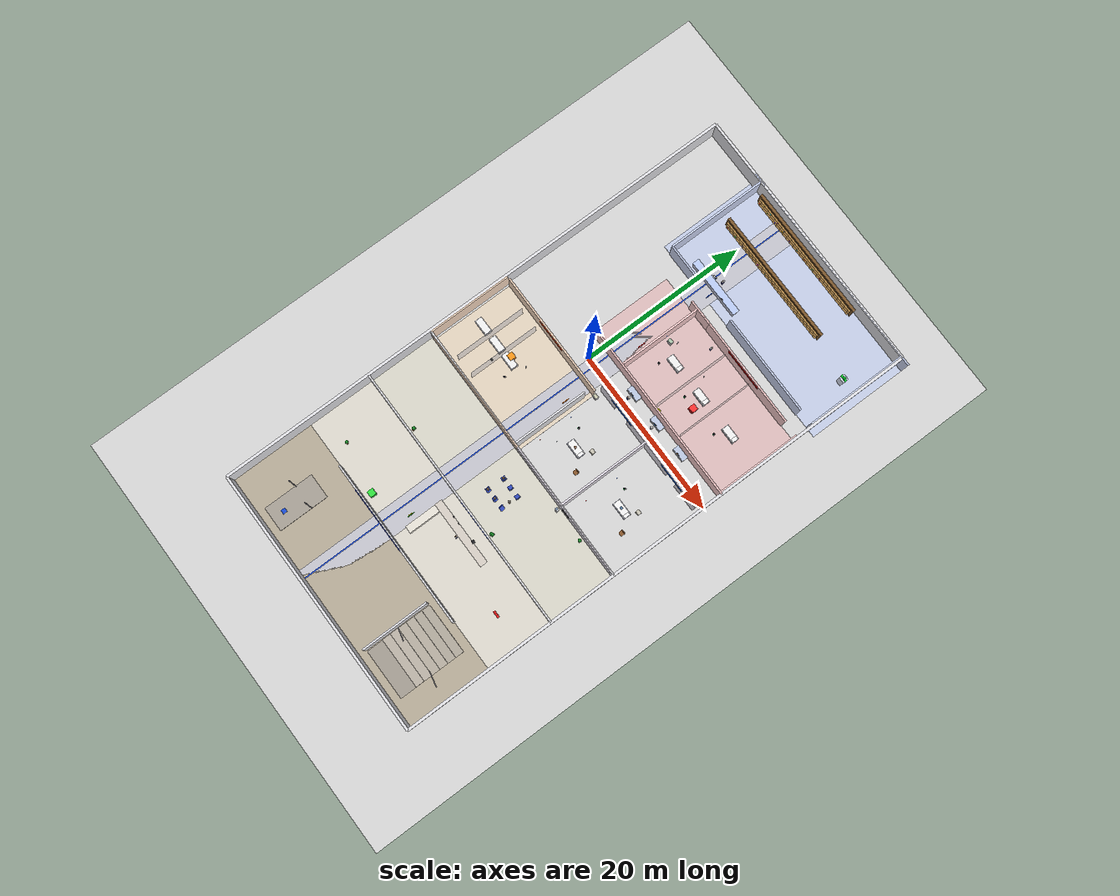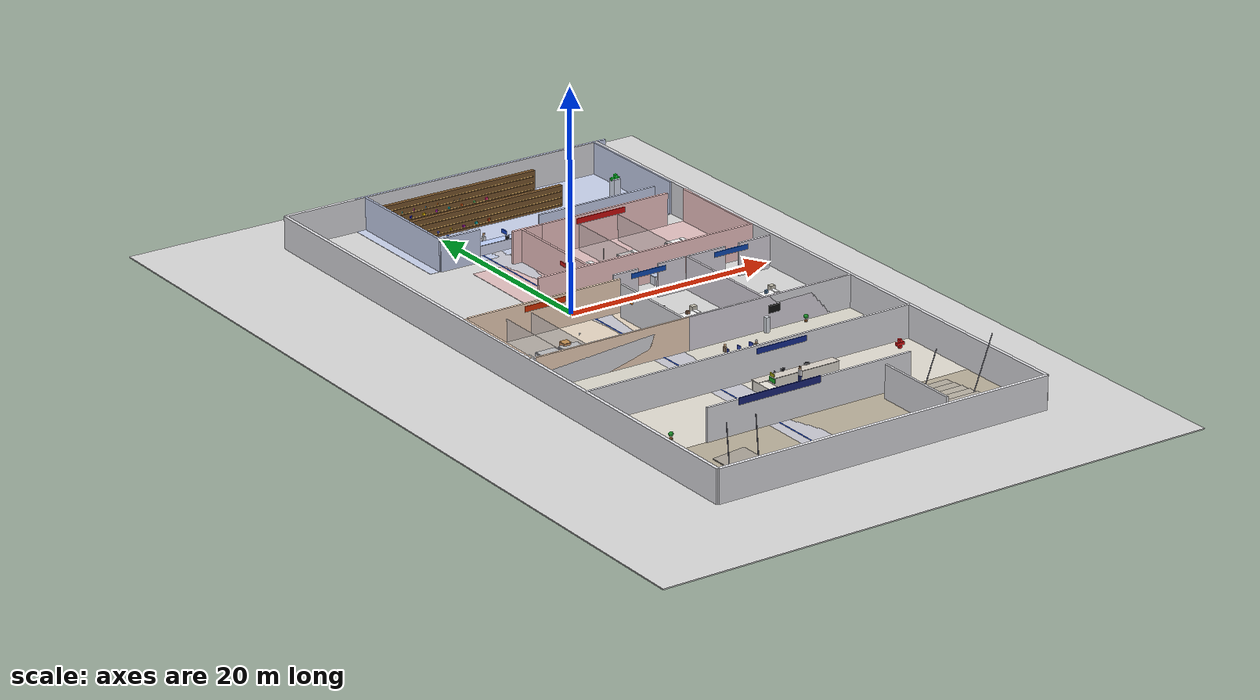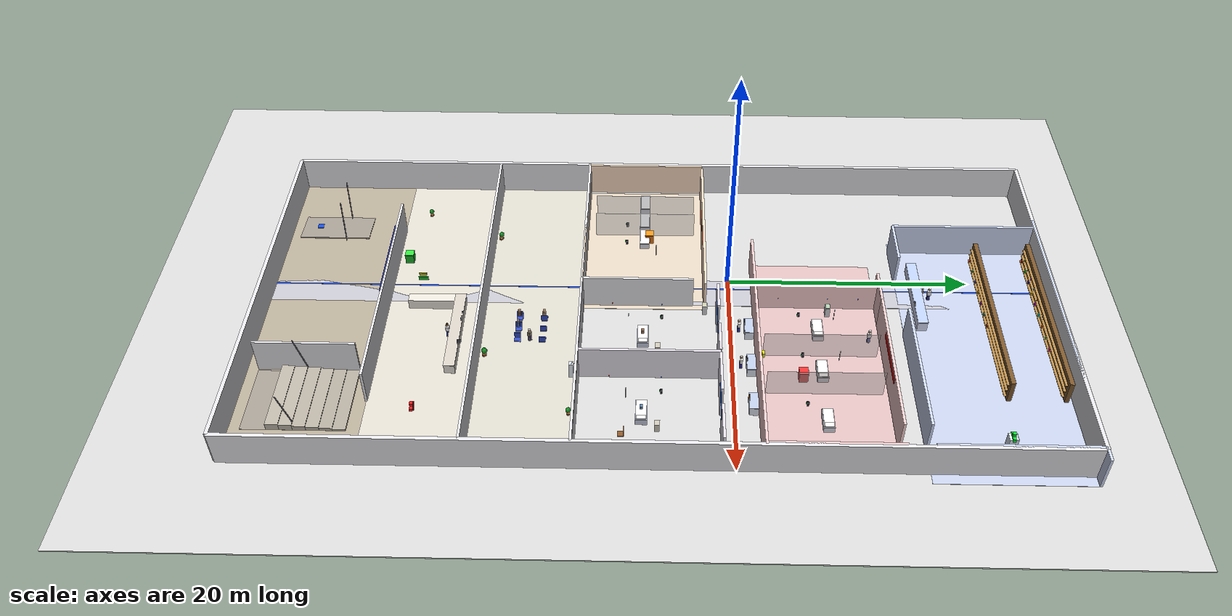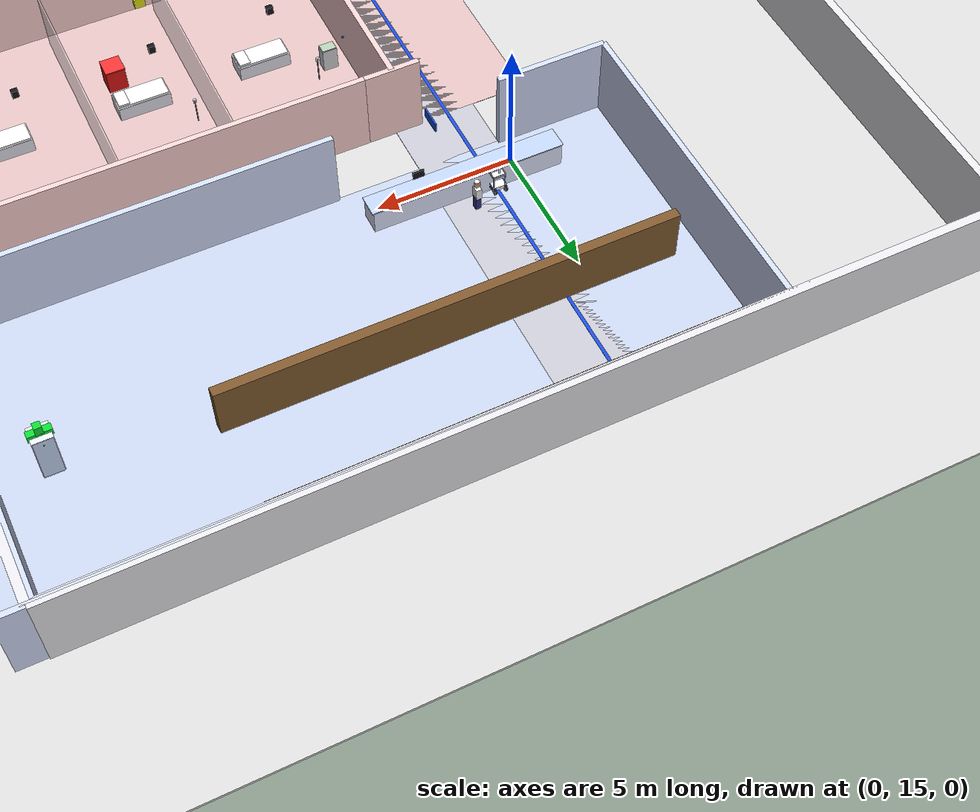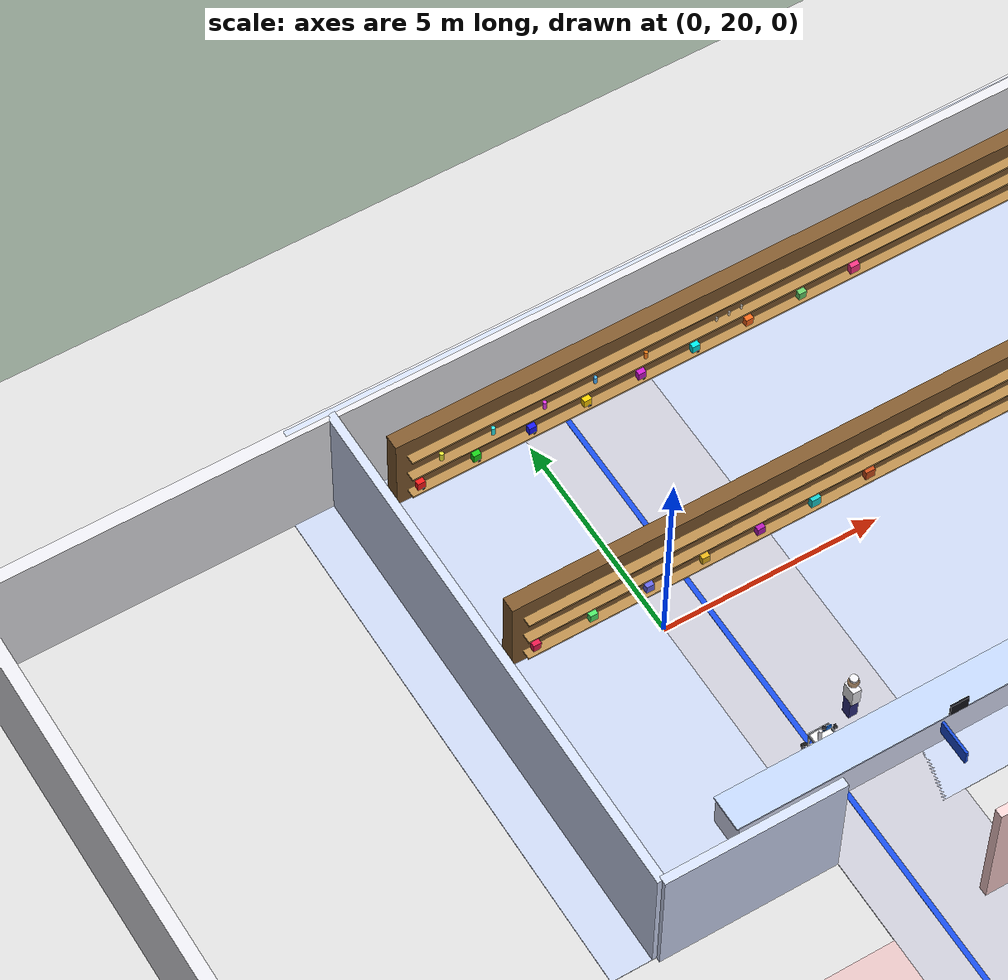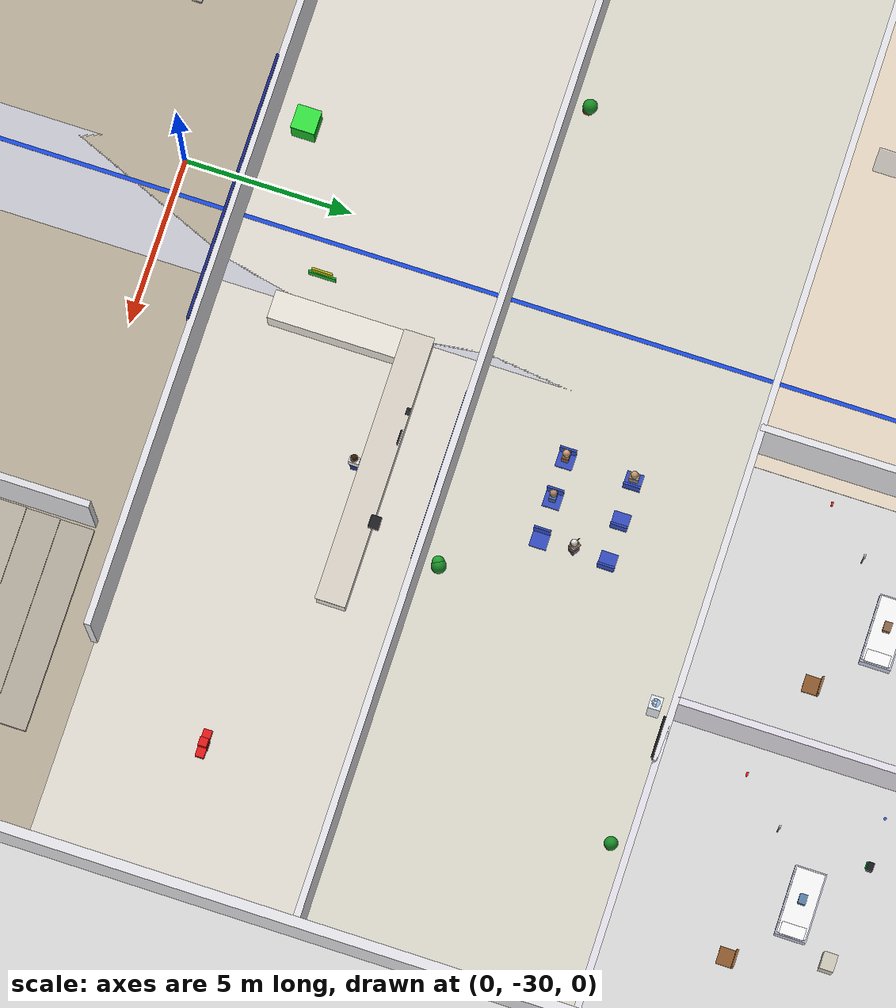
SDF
<?xml version="1.0"?>
<sdf version="1.9">
<world name="hospital">

  <plugin filename="ignition-gazebo-physics-system"
          name="ignition::gazebo::systems::Physics"/>
  <plugin filename="ignition-gazebo-user-commands-system"
          name="ignition::gazebo::systems::UserCommands"/>
  <plugin filename="ignition-gazebo-scene-broadcaster-system"
          name="ignition::gazebo::systems::SceneBroadcaster"/>
  <plugin filename="ignition-gazebo-sensors-system"
          name="ignition::gazebo::systems::Sensors">
    <render_engine>ogre2</render_engine>
  </plugin>

  <physics name="default_physics" default="true" type="ode">
    <max_step_size>0.001</max_step_size>
    <real_time_factor>1.0</real_time_factor>
    <real_time_update_rate>1000</real_time_update_rate>
  </physics>

  <light name="sun" type="directional">
    <pose>0 0 30 0 0 0</pose><cast_shadows>true</cast_shadows>
    <diffuse>0.9 0.9 0.9 1</diffuse><specular>0.2 0.2 0.2 1</specular>
    <direction>-0.3 0.1 -0.9</direction>
    <attenuation><range>1000</range><constant>0.9</constant><linear>0.01</linear><quadratic>0.001</quadratic></attenuation>
  </light>
  <light name="spot1" type="point"><pose>1 10 3 0 0 0</pose><diffuse>0.95 0.95 1 1</diffuse><specular>0.1 0.1 0.1 1</specular><attenuation><range>12</range><constant>0.4</constant><linear>0.05</linear><quadratic>0.002</quadratic></attenuation><cast_shadows>false</cast_shadows></light>
  <light name="spot2" type="point"><pose>1 -5 3 0 0 0</pose><diffuse>0.95 0.95 1 1</diffuse><specular>0.1 0.1 0.1 1</specular><attenuation><range>12</range><constant>0.4</constant><linear>0.05</linear><quadratic>0.002</quadratic></attenuation><cast_shadows>false</cast_shadows></light>
  <light name="spot3" type="point"><pose>1 -20 3 0 0 0</pose><diffuse>0.95 0.95 1 1</diffuse><specular>0.1 0.1 0.1 1</specular><attenuation><range>12</range><constant>0.4</constant><linear>0.05</linear><quadratic>0.002</quadratic></attenuation><cast_shadows>false</cast_shadows></light>
  <light name="spot4" type="point"><pose>8 20 3 0 0 0</pose><diffuse>0.8 0.9 1 1</diffuse><specular>0.1 0.1 0.2 1</specular><attenuation><range>14</range><constant>0.3</constant><linear>0.05</linear><quadratic>0.002</quadratic></attenuation><cast_shadows>false</cast_shadows></light>
  <light name="spot5" type="point"><pose>11 7 3 0 0 0</pose><diffuse>1 0.92 0.88 1</diffuse><specular>0.1 0.05 0.05 1</specular><attenuation><range>14</range><constant>0.3</constant><linear>0.05</linear><quadratic>0.002</quadratic></attenuation><cast_shadows>false</cast_shadows></light>
  <light name="spot6" type="point"><pose>-5 -7 3 0 0 0</pose><diffuse>1 0.95 0.85 1</diffuse><specular>0.1 0.08 0.05 1</specular><attenuation><range>14</range><constant>0.3</constant><linear>0.05</linear><quadratic>0.002</quadratic></attenuation><cast_shadows>false</cast_shadows></light>
  <light name="spot7" type="point"><pose>5 -23 3 0 0 0</pose><diffuse>1 0.98 0.95 1</diffuse><specular>0.1 0.1 0.1 1</specular><attenuation><range>14</range><constant>0.3</constant><linear>0.05</linear><quadratic>0.002</quadratic></attenuation><cast_shadows>false</cast_shadows></light>

  <!-- SOL -->
  <model name="floor"><static>true</static><pose>2 -8 -0.05 0 0 0</pose>
    <link name="l"><collision name="c"><geometry><box><size>52 80 0.1</size></box></geometry></collision>
    <visual name="v"><geometry><box><size>52 80 0.1</size></box></geometry>
    <material><ambient>0.85 0.85 0.85 1</ambient><diffuse>0.85 0.85 0.85 1</diffuse></material></visual></link></model>

  <!-- MURS EXTERIEURS -->
  <model name="mn"><static>true</static><pose>4 26 1.5 0 0 0</pose><link name="l"><collision name="c"><geometry><box><size>32 0.3 3</size></box></geometry></collision><visual name="v"><geometry><box><size>32 0.3 3</size></box></geometry><material><ambient>0.9 0.9 0.92 1</ambient><diffuse>0.9 0.9 0.92 1</diffuse></material></visual></link></model>
  <model name="ms"><static>true</static><pose>4 -38 1.5 0 0 0</pose><link name="l"><collision name="c"><geometry><box><size>32 0.3 3</size></box></geometry></collision><visual name="v"><geometry><box><size>32 0.3 3</size></box></geometry><material><ambient>0.9 0.9 0.92 1</ambient><diffuse>0.9 0.9 0.92 1</diffuse></material></visual></link></model>
  <model name="me"><static>true</static><pose>20 -6 1.5 0 0 0</pose><link name="l"><collision name="c"><geometry><box><size>0.3 64 3</size></box></geometry></collision><visual name="v"><geometry><box><size>0.3 64 3</size></box></geometry><material><ambient>0.9 0.9 0.92 1</ambient><diffuse>0.9 0.9 0.92 1</diffuse></material></visual></link></model>
  <model name="mo"><static>true</static><pose>-12 -6 1.5 0 0 0</pose><link name="l"><collision name="c"><geometry><box><size>0.3 64 3</size></box></geometry></collision><visual name="v"><geometry><box><size>0.3 64 3</size></box></geometry><material><ambient>0.9 0.9 0.92 1</ambient><diffuse>0.9 0.9 0.92 1</diffuse></material></visual></link></model>

  <!-- COULOIR PRINCIPAL (chemin robot x=0..3) -->
  <model name="couloir_sol"><static>true</static><pose>1.5 -6 0.01 0 0 0</pose>
    <link name="l"><visual name="v"><geometry><box><size>3 64 0.02</size></box></geometry>
    <material><ambient>0.78 0.78 0.82 1</ambient><diffuse>0.78 0.78 0.82 1</diffuse></material></visual></link></model>
  <model name="ligne_guide"><static>true</static><pose>1 -6 0.02 0 0 0</pose>
    <link name="l"><visual name="v"><geometry><box><size>0.12 64 0.005</size></box></geometry>
    <material><ambient>0.1 0.3 0.9 1</ambient><diffuse>0.1 0.3 0.9 1</diffuse><emissive>0.02 0.06 0.18 1</emissive></material></visual></link></model>

  <!-- ENTREE PRINCIPALE (y=-38..-28) -->
  <model name="entree_sol"><static>true</static><pose>4 -33 0.01 0 0 0</pose>
    <link name="l"><visual name="v"><geometry><box><size>32 10 0.02</size></box></geometry>
    <material><ambient>0.72 0.68 0.6 1</ambient><diffuse>0.72 0.68 0.6 1</diffuse></material></visual></link></model>

  <!-- Portes double entree -->
  <model name="porte_g"><static>true</static><pose>-0.5 -28 1.1 0 0 0</pose>
    <link name="l"><collision name="c"><geometry><box><size>1.8 0.1 2.2</size></box></geometry></collision>
    <visual name="v"><geometry><box><size>1.8 0.1 2.2</size></box></geometry>
    <material><ambient>0.25 0.45 0.65 1</ambient><diffuse>0.25 0.45 0.65 1</diffuse><specular>0.5 0.7 0.9 1</specular></material></visual></link></model>
  <model name="porte_d"><static>true</static><pose>2.5 -28 1.1 0 0 0</pose>
    <link name="l"><collision name="c"><geometry><box><size>1.8 0.1 2.2</size></box></geometry></collision>
    <visual name="v"><geometry><box><size>1.8 0.1 2.2</size></box></geometry>
    <material><ambient>0.25 0.45 0.65 1</ambient><diffuse>0.25 0.45 0.65 1</diffuse><specular>0.5 0.7 0.9 1</specular></material></visual></link></model>
  <model name="cadre_ph"><static>true</static><pose>1 -28 2.3 0 0 0</pose><link name="l"><visual name="v"><geometry><box><size>5 0.12 0.18</size></box></geometry><material><ambient>0.6 0.6 0.65 1</ambient><diffuse>0.6 0.6 0.65 1</diffuse></material></visual></link></model>
  <model name="enseigne_hop"><static>true</static><pose>1 -28.1 2.8 0 0 0</pose><link name="l">
    <visual name="v"><geometry><box><size>8 0.08 0.6</size></box></geometry>
    <material><ambient>0.1 0.15 0.5 1</ambient><diffuse>0.1 0.15 0.5 1</diffuse><emissive>0.04 0.06 0.2 1</emissive></material></visual></link></model>

  <!-- ESCALIERS vers 2e etage (cote est) -->
  <model name="esc_base"><static>true</static><pose>14 -33 0 0 0 0</pose>
    <link name="l"><collision name="c"><geometry><box><size>6 8 0.05</size></box></geometry></collision>
    <visual name="v"><geometry><box><size>6 8 0.05</size></box></geometry>
    <material><ambient>0.65 0.62 0.58 1</ambient><diffuse>0.65 0.62 0.58 1</diffuse></material></visual></link></model>
  <model name="m1"><static>true</static><pose>14 -29.5 0.1 0 0 0</pose><link name="l"><collision name="c"><geometry><box><size>6 1 0.18</size></box></geometry></collision><visual name="v"><geometry><box><size>6 1 0.18</size></box></geometry><material><ambient>0.7 0.67 0.62 1</ambient><diffuse>0.7 0.67 0.62 1</diffuse></material></visual></link></model>
  <model name="m2"><static>true</static><pose>14 -30.5 0.1 0 0 0</pose><link name="l"><collision name="c"><geometry><box><size>6 1 0.36</size></box></geometry></collision><visual name="v"><geometry><box><size>6 1 0.36</size></box></geometry><material><ambient>0.7 0.67 0.62 1</ambient><diffuse>0.7 0.67 0.62 1</diffuse></material></visual></link></model>
  <model name="m3"><static>true</static><pose>14 -31.5 0.1 0 0 0</pose><link name="l"><collision name="c"><geometry><box><size>6 1 0.54</size></box></geometry></collision><visual name="v"><geometry><box><size>6 1 0.54</size></box></geometry><material><ambient>0.72 0.69 0.64 1</ambient><diffuse>0.72 0.69 0.64 1</diffuse></material></visual></link></model>
  <model name="m4"><static>true</static><pose>14 -32.5 0.1 0 0 0</pose><link name="l"><collision name="c"><geometry><box><size>6 1 0.72</size></box></geometry></collision><visual name="v"><geometry><box><size>6 1 0.72</size></box></geometry><material><ambient>0.72 0.69 0.64 1</ambient><diffuse>0.72 0.69 0.64 1</diffuse></material></visual></link></model>
  <model name="m5"><static>true</static><pose>14 -33.5 0.1 0 0 0</pose><link name="l"><collision name="c"><geometry><box><size>6 1 0.90</size></box></geometry></collision><visual name="v"><geometry><box><size>6 1 0.90</size></box></geometry><material><ambient>0.74 0.71 0.66 1</ambient><diffuse>0.74 0.71 0.66 1</diffuse></material></visual></link></model>
  <model name="m6"><static>true</static><pose>14 -34.5 0.1 0 0 0</pose><link name="l"><collision name="c"><geometry><box><size>6 1 1.08</size></box></geometry></collision><visual name="v"><geometry><box><size>6 1 1.08</size></box></geometry><material><ambient>0.74 0.71 0.66 1</ambient><diffuse>0.74 0.71 0.66 1</diffuse></material></visual></link></model>
  <model name="rampe_g"><static>true</static><pose>11.2 -33 1.0 0 0.35 0</pose><link name="l"><visual name="v"><geometry><cylinder><radius>0.04</radius><length>9</length></cylinder></geometry><material><ambient>0.5 0.5 0.55 1</ambient><diffuse>0.5 0.5 0.55 1</diffuse></material></visual></link></model>
  <model name="rampe_d"><static>true</static><pose>16.8 -33 1.0 0 0.35 0</pose><link name="l"><visual name="v"><geometry><cylinder><radius>0.04</radius><length>9</length></cylinder></geometry><material><ambient>0.5 0.5 0.55 1</ambient><diffuse>0.5 0.5 0.55 1</diffuse></material></visual></link></model>
  <model name="mur_esc"><static>true</static><pose>10.8 -33 1.5 0 0 0</pose><link name="l"><collision name="c"><geometry><box><size>0.2 8 3</size></box></geometry></collision><visual name="v"><geometry><box><size>0.2 8 3</size></box></geometry><material><ambient>0.88 0.88 0.9 1</ambient><diffuse>0.88 0.88 0.9 1</diffuse></material></visual></link></model>

  <!-- ACCUEIL / RECEPTION (y=-28..-20) -->
  <model name="acc_sol"><static>true</static><pose>4 -24 0.01 0 0 0</pose>
    <link name="l"><visual name="v"><geometry><box><size>32 8 0.02</size></box></geometry>
    <material><ambient>0.88 0.86 0.82 1</ambient><diffuse>0.88 0.86 0.82 1</diffuse></material></visual></link></model>
  <model name="mur_acc_n"><static>true</static><pose>4 -20 1.5 0 0 0</pose><link name="l"><collision name="c"><geometry><box><size>32 0.2 3</size></box></geometry></collision><visual name="v"><geometry><box><size>32 0.2 3</size></box></geometry><material><ambient>0.9 0.9 0.92 1</ambient><diffuse>0.9 0.9 0.92 1</diffuse></material></visual></link></model>
  <model name="mur_acc_s"><static>true</static><pose>4 -28 1.5 0 0 0</pose><link name="l"><collision name="c"><geometry><box><size>20 0.2 3</size></box></geometry></collision><visual name="v"><geometry><box><size>20 0.2 3</size></box></geometry><material><ambient>0.9 0.9 0.92 1</ambient><diffuse>0.9 0.9 0.92 1</diffuse></material></visual></link></model>

  <!-- Comptoir reception -->
  <model name="cpt1"><static>true</static><pose>7 -22 0.45 0 0 0</pose>
    <link name="l"><collision name="c"><geometry><box><size>8 0.85 0.9</size></box></geometry></collision>
    <visual name="v"><geometry><box><size>8 0.85 0.9</size></box></geometry><material><ambient>0.92 0.9 0.86 1</ambient><diffuse>0.92 0.9 0.86 1</diffuse></material></visual>
    <visual name="dessus"><pose>0 0 0.47 0 0 0</pose><geometry><box><size>8.1 0.9 0.04</size></box></geometry><material><ambient>0.85 0.82 0.78 1</ambient><diffuse>0.85 0.82 0.78 1</diffuse></material></visual></link></model>
  <model name="cpt2"><static>true</static><pose>3.4 -24 0.45 0 0 0</pose>
    <link name="l"><collision name="c"><geometry><box><size>0.85 4.5 0.9</size></box></geometry></collision>
    <visual name="v"><geometry><box><size>0.85 4.5 0.9</size></box></geometry><material><ambient>0.92 0.9 0.86 1</ambient><diffuse>0.92 0.9 0.86 1</diffuse></material></visual></link></model>

  <!-- Ordinateur accueil -->
  <model name="pc_acc"><static>true</static><pose>6 -21.6 1.08 0 0 0</pose><link name="l">
    <visual name="ecran"><geometry><box><size>0.4 0.04 0.3</size></box></geometry><material><ambient>0.08 0.08 0.1 1</ambient><diffuse>0.08 0.08 0.1 1</diffuse></material></visual>
    <visual name="glow"><geometry><box><size>0.36 0.02 0.26</size></box></geometry><material><ambient>0.15 0.5 0.9 1</ambient><diffuse>0.15 0.5 0.9 1</diffuse><emissive>0.06 0.2 0.4 1</emissive></material></visual>
  </link></model>

  <model name="sign_acc"><static>true</static><pose>7 -20.1 2.5 0 0 0</pose><link name="l">
    <visual name="v"><geometry><box><size>5 0.06 0.5</size></box></geometry>
    <material><ambient>0.08 0.18 0.6 1</ambient><diffuse>0.08 0.18 0.6 1</diffuse><emissive>0.03 0.08 0.25 1</emissive></material></visual></link></model>

  <!-- Croix medicale -->
  <model name="cx_h"><static>true</static><pose>16 -24 1.8 0 0 0</pose><link name="l"><visual name="v"><geometry><box><size>0.8 0.25 0.25</size></box></geometry><material><ambient>0.9 0.1 0.1 1</ambient><diffuse>0.9 0.1 0.1 1</diffuse><emissive>0.3 0 0 1</emissive></material></visual></link></model>
  <model name="cx_v"><static>true</static><pose>16 -24 1.8 0 0 0</pose><link name="l"><visual name="v"><geometry><box><size>0.25 0.25 0.8</size></box></geometry><material><ambient>0.9 0.1 0.1 1</ambient><diffuse>0.9 0.1 0.1 1</diffuse><emissive>0.3 0 0 1</emissive></material></visual></link></model>

  <!-- Assistante accueil -->
  <model name="assistante"><static>true</static><pose>7 -22.6 0 0 0 -1.57</pose><link name="l">
    <visual name="j"><pose>0 0 0.42 0 0 0</pose><geometry><box><size>0.22 0.2 0.55</size></box></geometry><material><ambient>0.15 0.2 0.5 1</ambient><diffuse>0.15 0.2 0.5 1</diffuse></material></visual>
    <visual name="t"><pose>0 0 0.9 0 0 0</pose><geometry><box><size>0.3 0.2 0.45</size></box></geometry><material><ambient>0.9 0.9 0.92 1</ambient><diffuse>0.9 0.9 0.92 1</diffuse></material></visual>
    <visual name="h"><pose>0 0 1.28 0 0 0</pose><geometry><sphere><radius>0.12</radius></sphere></geometry><material><ambient>0.82 0.65 0.5 1</ambient><diffuse>0.82 0.65 0.5 1</diffuse></material></visual>
    <visual name="cv"><pose>0 0 1.4 0 0 0</pose><geometry><sphere><radius>0.1</radius></sphere></geometry><material><ambient>0.2 0.12 0.05 1</ambient><diffuse>0.2 0.12 0.05 1</diffuse></material></visual>
    <collision name="c"><pose>0 0 0.75 0 0 0</pose><geometry><box><size>0.35 0.25 1.5</size></box></geometry></collision>
  </link></model>

  <!-- SALLE D'ATTENTE (y=-20..-12) -->
  <model name="att_sol"><static>true</static><pose>4 -16 0.01 0 0 0</pose>
    <link name="l"><visual name="v"><geometry><box><size>32 8 0.02</size></box></geometry>
    <material><ambient>0.86 0.85 0.8 1</ambient><diffuse>0.86 0.85 0.8 1</diffuse></material></visual></link></model>
  <model name="mur_att_n"><static>true</static><pose>4 -12 1.5 0 0 0</pose><link name="l"><collision name="c"><geometry><box><size>32 0.2 3</size></box></geometry></collision><visual name="v"><geometry><box><size>32 0.2 3</size></box></geometry><material><ambient>0.9 0.9 0.92 1</ambient><diffuse>0.9 0.9 0.92 1</diffuse></material></visual></link></model>

  <!-- Chaises salle d'attente -->
  <model name="ch1"><static>true</static><pose>5 -17 0.22 0 0 0</pose><link name="l"><collision name="c"><geometry><box><size>0.55 0.55 0.44</size></box></geometry></collision><visual name="s"><geometry><box><size>0.5 0.5 0.08</size></box></geometry><material><ambient>0.2 0.3 0.75 1</ambient><diffuse>0.2 0.3 0.75 1</diffuse></material></visual><visual name="d"><pose>-0.22 0 0.3 0 0 0</pose><geometry><box><size>0.06 0.5 0.55</size></box></geometry><material><ambient>0.2 0.3 0.75 1</ambient><diffuse>0.2 0.3 0.75 1</diffuse></material></visual></link></model>
  <model name="ch2"><static>true</static><pose>6.2 -17 0.22 0 0 0</pose><link name="l"><collision name="c"><geometry><box><size>0.55 0.55 0.44</size></box></geometry></collision><visual name="s"><geometry><box><size>0.5 0.5 0.08</size></box></geometry><material><ambient>0.2 0.3 0.75 1</ambient><diffuse>0.2 0.3 0.75 1</diffuse></material></visual><visual name="d"><pose>-0.22 0 0.3 0 0 0</pose><geometry><box><size>0.06 0.5 0.55</size></box></geometry><material><ambient>0.2 0.3 0.75 1</ambient><diffuse>0.2 0.3 0.75 1</diffuse></material></visual></link></model>
  <model name="ch3"><static>true</static><pose>7.4 -17 0.22 0 0 0</pose><link name="l"><collision name="c"><geometry><box><size>0.55 0.55 0.44</size></box></geometry></collision><visual name="s"><geometry><box><size>0.5 0.5 0.08</size></box></geometry><material><ambient>0.2 0.3 0.75 1</ambient><diffuse>0.2 0.3 0.75 1</diffuse></material></visual><visual name="d"><pose>-0.22 0 0.3 0 0 0</pose><geometry><box><size>0.06 0.5 0.55</size></box></geometry><material><ambient>0.2 0.3 0.75 1</ambient><diffuse>0.2 0.3 0.75 1</diffuse></material></visual></link></model>
  <model name="ch4"><static>true</static><pose>5 -15 0.22 0 0 0</pose><link name="l"><collision name="c"><geometry><box><size>0.55 0.55 0.44</size></box></geometry></collision><visual name="s"><geometry><box><size>0.5 0.5 0.08</size></box></geometry><material><ambient>0.2 0.3 0.75 1</ambient><diffuse>0.2 0.3 0.75 1</diffuse></material></visual><visual name="d"><pose>0.22 0 0.3 0 0 0</pose><geometry><box><size>0.06 0.5 0.55</size></box></geometry><material><ambient>0.2 0.3 0.75 1</ambient><diffuse>0.2 0.3 0.75 1</diffuse></material></visual></link></model>
  <model name="ch5"><static>true</static><pose>6.2 -15 0.22 0 0 0</pose><link name="l"><collision name="c"><geometry><box><size>0.55 0.55 0.44</size></box></geometry></collision><visual name="s"><geometry><box><size>0.5 0.5 0.08</size></box></geometry><material><ambient>0.2 0.3 0.75 1</ambient><diffuse>0.2 0.3 0.75 1</diffuse></material></visual><visual name="d"><pose>0.22 0 0.3 0 0 0</pose><geometry><box><size>0.06 0.5 0.55</size></box></geometry><material><ambient>0.2 0.3 0.75 1</ambient><diffuse>0.2 0.3 0.75 1</diffuse></material></visual></link></model>
  <model name="ch6"><static>true</static><pose>7.4 -15 0.22 0 0 0</pose><link name="l"><collision name="c"><geometry><box><size>0.55 0.55 0.44</size></box></geometry></collision><visual name="s"><geometry><box><size>0.5 0.5 0.08</size></box></geometry><material><ambient>0.2 0.3 0.75 1</ambient><diffuse>0.2 0.3 0.75 1</diffuse></material></visual><visual name="d"><pose>0.22 0 0.3 0 0 0</pose><geometry><box><size>0.06 0.5 0.55</size></box></geometry><material><ambient>0.2 0.3 0.75 1</ambient><diffuse>0.2 0.3 0.75 1</diffuse></material></visual></link></model>

  <!-- Patients assis -->
  <model name="pa1"><static>true</static><pose>5 -17 0.44 0 0 0</pose><link name="l"><visual name="c"><pose>0 0 0.35 0 0 0</pose><geometry><box><size>0.28 0.2 0.42</size></box></geometry><material><ambient>0.5 0.35 0.2 1</ambient><diffuse>0.5 0.35 0.2 1</diffuse></material></visual><visual name="h"><pose>0 0 0.72 0 0 0</pose><geometry><sphere><radius>0.11</radius></sphere></geometry><material><ambient>0.8 0.62 0.48 1</ambient><diffuse>0.8 0.62 0.48 1</diffuse></material></visual></link></model>
  <model name="pa2"><static>true</static><pose>6.2 -17 0.44 0 0 0</pose><link name="l"><visual name="c"><pose>0 0 0.35 0 0 0</pose><geometry><box><size>0.28 0.2 0.42</size></box></geometry><material><ambient>0.3 0.4 0.6 1</ambient><diffuse>0.3 0.4 0.6 1</diffuse></material></visual><visual name="h"><pose>0 0 0.72 0 0 0</pose><geometry><sphere><radius>0.11</radius></sphere></geometry><material><ambient>0.68 0.52 0.4 1</ambient><diffuse>0.68 0.52 0.4 1</diffuse></material></visual></link></model>
  <model name="pa3"><static>true</static><pose>5 -15 0.44 0 0 1.57</pose><link name="l"><visual name="c"><pose>0 0 0.35 0 0 0</pose><geometry><box><size>0.28 0.2 0.42</size></box></geometry><material><ambient>0.6 0.5 0.4 1</ambient><diffuse>0.6 0.5 0.4 1</diffuse></material></visual><visual name="h"><pose>0 0 0.72 0 0 0</pose><geometry><sphere><radius>0.11</radius></sphere></geometry><material><ambient>0.75 0.6 0.45 1</ambient><diffuse>0.75 0.6 0.45 1</diffuse></material></visual></link></model>

  <!-- TV salle d'attente -->
  <model name="tv_att"><static>true</static><pose>12 -12.1 1.8 0.1 0 0</pose><link name="l"><visual name="c"><geometry><box><size>1.2 0.08 0.7</size></box></geometry><material><ambient>0.08 0.08 0.08 1</ambient><diffuse>0.08 0.08 0.08 1</diffuse></material></visual><visual name="e"><geometry><box><size>1.12 0.06 0.62</size></box></geometry><material><ambient>0.05 0.2 0.45 1</ambient><diffuse>0.05 0.2 0.45 1</diffuse><emissive>0.02 0.08 0.18 1</emissive></material></visual></link></model>

  <!-- URGENCES (y=-12..-2) -->
  <model name="mur_sep_u"><static>true</static><pose>3 -7.5 1.5 0 0 0</pose><link name="l"><collision name="c"><geometry><box><size>0.2 9.1 3</size></box></geometry></collision><visual name="v"><geometry><box><size>0.2 9.1 3</size></box></geometry><material><ambient>0.9 0.9 0.92 1</ambient><diffuse>0.9 0.9 0.92 1</diffuse></material></visual></link></model>
  <model name="urg_sol"><static>true</static><pose>-4 -7 0.01 0 0 0</pose>
    <link name="l"><visual name="v"><geometry><box><size>15 10 0.02</size></box></geometry>
    <material><ambient>0.9 0.84 0.76 1</ambient><diffuse>0.9 0.84 0.76 1</diffuse></material></visual></link></model>
  <model name="urg_n"><static>true</static><pose>-4 -2 1.5 0 0 0</pose><link name="l"><collision name="c"><geometry><box><size>15 0.2 3</size></box></geometry></collision><visual name="v"><geometry><box><size>15 0.2 3</size></box></geometry><material><ambient>1 0.88 0.78 1</ambient><diffuse>1 0.88 0.78 1</diffuse></material></visual></link></model>
  <model name="urg_s"><static>true</static><pose>-4 -12 1.5 0 0 0</pose><link name="l"><collision name="c"><geometry><box><size>15 0.2 3</size></box></geometry></collision><visual name="v"><geometry><box><size>15 0.2 3</size></box></geometry><material><ambient>1 0.88 0.78 1</ambient><diffuse>1 0.88 0.78 1</diffuse></material></visual></link></model>
  <model name="urg_o"><static>true</static><pose>-11.8 -7 1.5 0 0 0</pose><link name="l"><collision name="c"><geometry><box><size>0.2 10 3</size></box></geometry></collision><visual name="v"><geometry><box><size>0.2 10 3</size></box></geometry><material><ambient>1 0.88 0.78 1</ambient><diffuse>1 0.88 0.78 1</diffuse></material></visual></link></model>
  <model name="sign_urg"><static>true</static><pose>-4 -2.1 2.5 0 0 0</pose><link name="l"><visual name="v"><geometry><box><size>4 0.06 0.5</size></box></geometry><material><ambient>0.9 0.2 0 1</ambient><diffuse>0.9 0.2 0 1</diffuse><emissive>0.35 0.05 0 1</emissive></material></visual></link></model>

  <!-- Rideaux separateurs urgences -->
  <model name="rid_u1"><static>true</static><pose>-5.8 -7 1.2 0 0 0</pose><link name="l"><visual name="v"><geometry><box><size>0.04 8.5 2.4</size></box></geometry><material><ambient>0.85 0.85 0.88 0.5</ambient><diffuse>0.85 0.85 0.88 0.5</diffuse></material></visual></link></model>
  <model name="rid_u2"><static>true</static><pose>-8.2 -7 1.2 0 0 0</pose><link name="l"><visual name="v"><geometry><box><size>0.04 8.5 2.4</size></box></geometry><material><ambient>0.85 0.85 0.88 0.5</ambient><diffuse>0.85 0.85 0.88 0.5</diffuse></material></visual></link></model>

  <!-- Lits urgences -->
  <model name="lit_u1"><static>true</static><pose>-4.8 -7 0.38 0 0 0</pose><link name="l"><collision name="c"><geometry><box><size>1.9 0.85 0.52</size></box></geometry></collision><visual name="c"><geometry><box><size>1.9 0.85 0.52</size></box></geometry><material><ambient>0.88 0.88 0.92 1</ambient><diffuse>0.88 0.88 0.92 1</diffuse></material></visual><visual name="mat"><pose>0 0 0.28 0 0 0</pose><geometry><box><size>1.82 0.78 0.1</size></box></geometry><material><ambient>0.96 0.96 0.96 1</ambient><diffuse>0.96 0.96 0.96 1</diffuse></material></visual></link></model>
  <model name="lit_u2"><static>true</static><pose>-7 -7 0.38 0 0 0</pose><link name="l"><collision name="c"><geometry><box><size>1.9 0.85 0.52</size></box></geometry></collision><visual name="c"><geometry><box><size>1.9 0.85 0.52</size></box></geometry><material><ambient>0.88 0.88 0.92 1</ambient><diffuse>0.88 0.88 0.92 1</diffuse></material></visual><visual name="mat"><pose>0 0 0.28 0 0 0</pose><geometry><box><size>1.82 0.78 0.1</size></box></geometry><material><ambient>0.96 0.96 0.96 1</ambient><diffuse>0.96 0.96 0.96 1</diffuse></material></visual></link></model>
  <model name="lit_u3"><static>true</static><pose>-9.5 -7 0.38 0 0 0</pose><link name="l"><collision name="c"><geometry><box><size>1.9 0.85 0.52</size></box></geometry></collision><visual name="c"><geometry><box><size>1.9 0.85 0.52</size></box></geometry><material><ambient>0.88 0.88 0.92 1</ambient><diffuse>0.88 0.88 0.92 1</diffuse></material></visual><visual name="mat"><pose>0 0 0.28 0 0 0</pose><geometry><box><size>1.82 0.78 0.1</size></box></geometry><material><ambient>0.96 0.96 0.96 1</ambient><diffuse>0.96 0.96 0.96 1</diffuse></material></visual></link></model>

  <!-- Moniteurs + perfusions urgences -->
  <model name="mon_u1"><static>true</static><pose>-3.6 -8.5 1.1 0 0 0</pose><link name="l"><visual name="c"><geometry><box><size>0.22 0.18 0.28</size></box></geometry><material><ambient>0.1 0.1 0.12 1</ambient><diffuse>0.1 0.1 0.12 1</diffuse></material></visual><visual name="e"><pose>0 -0.1 0.02 0.3 0 0</pose><geometry><box><size>0.18 0.02 0.2</size></box></geometry><material><ambient>0 0.75 0.2 1</ambient><diffuse>0 0.75 0.2 1</diffuse><emissive>0 0.35 0.08 1</emissive></material></visual></link></model>
  <model name="mon_u2"><static>true</static><pose>-5.9 -8.5 1.1 0 0 0</pose><link name="l"><visual name="c"><geometry><box><size>0.22 0.18 0.28</size></box></geometry><material><ambient>0.1 0.1 0.12 1</ambient><diffuse>0.1 0.1 0.12 1</diffuse></material></visual><visual name="e"><pose>0 -0.1 0.02 0.3 0 0</pose><geometry><box><size>0.18 0.02 0.2</size></box></geometry><material><ambient>0 0.75 0.2 1</ambient><diffuse>0 0.75 0.2 1</diffuse><emissive>0 0.35 0.08 1</emissive></material></visual></link></model>
  <model name="iv_u1"><static>true</static><pose>-3.2 -6 1.0 0 0 0</pose><link name="l"><visual name="p"><pose>0 0 -0.7 0 0 0</pose><geometry><cylinder><radius>0.02</radius><length>1.4</length></cylinder></geometry><material><ambient>0.5 0.5 0.5 1</ambient><diffuse>0.5 0.5 0.5 1</diffuse></material></visual><visual name="s"><geometry><box><size>0.1 0.06 0.16</size></box></geometry><material><ambient>0.8 0.9 1 0.6</ambient><diffuse>0.8 0.9 1 0.6</diffuse></material></visual></link></model>

  <!-- TABLE LIVRAISON URGENCES -->
  <model name="delivery_urg"><static>true</static><pose>-5.0 -6.6 0.45 0 0 0</pose>
    <link name="l"><collision name="c"><geometry><box><size>0.7 0.7 0.9</size></box></geometry></collision>
    <visual name="v"><geometry><box><size>0.7 0.7 0.9</size></box></geometry><material><ambient>0.9 0.45 0.05 1</ambient><diffuse>0.9 0.45 0.05 1</diffuse></material></visual>
    <visual name="top"><pose>0 0 0.47 0 0 0</pose><geometry><box><size>0.72 0.72 0.04</size></box></geometry>
    <material><ambient>1 0.6 0.1 1</ambient><diffuse>1 0.6 0.1 1</diffuse><emissive>0.2 0.08 0 1</emissive></material></visual></link></model>

  <!-- REANIMATION (y=2..12) -->
  <model name="re_sol"><static>true</static><pose>9 7 0.01 0 0 0</pose>
    <link name="l"><visual name="v"><geometry><box><size>22 10 0.02</size></box></geometry>
    <material><ambient>0.88 0.75 0.75 1</ambient><diffuse>0.88 0.75 0.75 1</diffuse></material></visual></link></model>
  <model name="re_n_l"><static>true</static><pose>3.5 12 1.5 0 0 0</pose><link name="l"><collision name="c"><geometry><box><size>3 0.2 3</size></box></geometry></collision><visual name="v"><geometry><box><size>3 0.2 3</size></box></geometry><material><ambient>1 0.82 0.82 1</ambient><diffuse>1 0.82 0.82 1</diffuse></material></visual></link></model>
  <model name="re_n_r"><static>true</static><pose>11 12 1.5 0 0 0</pose><link name="l"><collision name="c"><geometry><box><size>14 0.2 3</size></box></geometry></collision><visual name="v"><geometry><box><size>14 0.2 3</size></box></geometry><material><ambient>1 0.82 0.82 1</ambient><diffuse>1 0.82 0.82 1</diffuse></material></visual></link></model>
  <model name="re_s"><static>true</static><pose>9 2 1.5 0 0 0</pose><link name="l"><collision name="c"><geometry><box><size>22 0.2 3</size></box></geometry></collision><visual name="v"><geometry><box><size>22 0.2 3</size></box></geometry><material><ambient>1 0.82 0.82 1</ambient><diffuse>1 0.82 0.82 1</diffuse></material></visual></link></model>
  <model name="re_e"><static>true</static><pose>19.8 7 1.5 0 0 0</pose><link name="l"><collision name="c"><geometry><box><size>0.2 10 3</size></box></geometry></collision><visual name="v"><geometry><box><size>0.2 10 3</size></box></geometry><material><ambient>1 0.82 0.82 1</ambient><diffuse>1 0.82 0.82 1</diffuse></material></visual></link></model>
  <model name="re_o"><static>true</static><pose>3 7 1.5 0 0 0</pose><link name="l"><collision name="c"><geometry><box><size>0.2 10 3</size></box></geometry></collision><visual name="v"><geometry><box><size>0.2 10 3</size></box></geometry><material><ambient>1 0.82 0.82 1</ambient><diffuse>1 0.82 0.82 1</diffuse></material></visual></link></model>
  <model name="sign_re"><static>true</static><pose>11 11.9 2.5 0 0 0</pose><link name="l"><visual name="v"><geometry><box><size>5 0.06 0.5</size></box></geometry><material><ambient>0.85 0.05 0.05 1</ambient><diffuse>0.85 0.05 0.05 1</diffuse><emissive>0.35 0 0 1</emissive></material></visual></link></model>

  <!-- Rideaux + lits réanimation -->
  <model name="rid_r1"><static>true</static><pose>8.5 7 1.2 0 0 0</pose><link name="l"><visual name="v"><geometry><box><size>0.04 9 2.4</size></box></geometry><material><ambient>0.88 0.82 0.82 0.5</ambient><diffuse>0.88 0.82 0.82 0.5</diffuse></material></visual></link></model>
  <model name="rid_r2"><static>true</static><pose>12.5 7 1.2 0 0 0</pose><link name="l"><visual name="v"><geometry><box><size>0.04 9 2.4</size></box></geometry><material><ambient>0.88 0.82 0.82 0.5</ambient><diffuse>0.88 0.82 0.82 0.5</diffuse></material></visual></link></model>

  <model name="lit_r1"><static>true</static><pose>6 7 0.38 0 0 0</pose><link name="l"><collision name="c"><geometry><box><size>1.9 0.85 0.52</size></box></geometry></collision><visual name="c"><geometry><box><size>1.9 0.85 0.52</size></box></geometry><material><ambient>0.88 0.88 0.92 1</ambient><diffuse>0.88 0.88 0.92 1</diffuse></material></visual><visual name="m"><pose>0 0 0.28 0 0 0</pose><geometry><box><size>1.82 0.78 0.1</size></box></geometry><material><ambient>0.96 0.96 0.96 1</ambient><diffuse>0.96 0.96 0.96 1</diffuse></material></visual><visual name="o"><pose>0.7 0 0.34 0 0 0</pose><geometry><box><size>0.4 0.7 0.07</size></box></geometry><material><ambient>0.98 0.98 0.98 1</ambient><diffuse>0.98 0.98 0.98 1</diffuse></material></visual></link></model>
  <model name="lit_r2"><static>true</static><pose>10.5 7 0.38 0 0 0</pose><link name="l"><collision name="c"><geometry><box><size>1.9 0.85 0.52</size></box></geometry></collision><visual name="c"><geometry><box><size>1.9 0.85 0.52</size></box></geometry><material><ambient>0.88 0.88 0.92 1</ambient><diffuse>0.88 0.88 0.92 1</diffuse></material></visual><visual name="m"><pose>0 0 0.28 0 0 0</pose><geometry><box><size>1.82 0.78 0.1</size></box></geometry><material><ambient>0.96 0.96 0.96 1</ambient><diffuse>0.96 0.96 0.96 1</diffuse></material></visual><visual name="o"><pose>0.7 0 0.34 0 0 0</pose><geometry><box><size>0.4 0.7 0.07</size></box></geometry><material><ambient>0.98 0.98 0.98 1</ambient><diffuse>0.98 0.98 0.98 1</diffuse></material></visual></link></model>
  <model name="lit_r3"><static>true</static><pose>15.5 7 0.38 0 0 0</pose><link name="l"><collision name="c"><geometry><box><size>1.9 0.85 0.52</size></box></geometry></collision><visual name="c"><geometry><box><size>1.9 0.85 0.52</size></box></geometry><material><ambient>0.88 0.88 0.92 1</ambient><diffuse>0.88 0.88 0.92 1</diffuse></material></visual><visual name="m"><pose>0 0 0.28 0 0 0</pose><geometry><box><size>1.82 0.78 0.1</size></box></geometry><material><ambient>0.96 0.96 0.96 1</ambient><diffuse>0.96 0.96 0.96 1</diffuse></material></visual><visual name="o"><pose>0.7 0 0.34 0 0 0</pose><geometry><box><size>0.4 0.7 0.07</size></box></geometry><material><ambient>0.98 0.98 0.98 1</ambient><diffuse>0.98 0.98 0.98 1</diffuse></material></visual></link></model>

  <!-- Moniteurs réa + perfusions -->
  <model name="mon_r1"><static>true</static><pose>5.0 5.5 1.1 0 0 0</pose><link name="l"><visual name="c"><geometry><box><size>0.24 0.18 0.3</size></box></geometry><material><ambient>0.08 0.08 0.1 1</ambient><diffuse>0.08 0.08 0.1 1</diffuse></material></visual><visual name="e"><pose>0 -0.1 0 0.3 0 0</pose><geometry><box><size>0.2 0.02 0.22</size></box></geometry><material><ambient>0 0.8 0.25 1</ambient><diffuse>0 0.8 0.25 1</diffuse><emissive>0 0.35 0.1 1</emissive></material></visual></link></model>
  <model name="mon_r2"><static>true</static><pose>9.5 5.5 1.1 0 0 0</pose><link name="l"><visual name="c"><geometry><box><size>0.24 0.18 0.3</size></box></geometry><material><ambient>0.08 0.08 0.1 1</ambient><diffuse>0.08 0.08 0.1 1</diffuse></material></visual><visual name="e"><pose>0 -0.1 0 0.3 0 0</pose><geometry><box><size>0.2 0.02 0.22</size></box></geometry><material><ambient>0 0.8 0.25 1</ambient><diffuse>0 0.8 0.25 1</diffuse><emissive>0 0.35 0.1 1</emissive></material></visual></link></model>
  <model name="mon_r3"><static>true</static><pose>14.5 5.5 1.1 0 0 0</pose><link name="l"><visual name="c"><geometry><box><size>0.24 0.18 0.3</size></box></geometry><material><ambient>0.08 0.08 0.1 1</ambient><diffuse>0.08 0.08 0.1 1</diffuse></material></visual><visual name="e"><pose>0 -0.1 0 0.3 0 0</pose><geometry><box><size>0.2 0.02 0.22</size></box></geometry><material><ambient>0 0.8 0.25 1</ambient><diffuse>0 0.8 0.25 1</diffuse><emissive>0 0.35 0.1 1</emissive></material></visual></link></model>
  <model name="iv_r1"><static>true</static><pose>4.4 8.5 1.0 0 0 0</pose><link name="l"><visual name="p"><pose>0 0 -0.7 0 0 0</pose><geometry><cylinder><radius>0.02</radius><length>1.4</length></cylinder></geometry><material><ambient>0.5 0.5 0.5 1</ambient><diffuse>0.5 0.5 0.5 1</diffuse></material></visual><visual name="s"><geometry><box><size>0.1 0.06 0.16</size></box></geometry><material><ambient>0.8 0.9 1 0.6</ambient><diffuse>0.8 0.9 1 0.6</diffuse></material></visual></link></model>
  <model name="iv_r2"><static>true</static><pose>9.0 8.5 1.0 0 0 0</pose><link name="l"><visual name="p"><pose>0 0 -0.7 0 0 0</pose><geometry><cylinder><radius>0.02</radius><length>1.4</length></cylinder></geometry><material><ambient>0.5 0.5 0.5 1</ambient><diffuse>0.5 0.5 0.5 1</diffuse></material></visual><visual name="s"><geometry><box><size>0.1 0.06 0.16</size></box></geometry><material><ambient>0.8 0.9 1 0.6</ambient><diffuse>0.8 0.9 1 0.6</diffuse></material></visual></link></model>

  <!-- Infirmiere réa -->
  <model name="inf_re"><static>true</static><pose>7 11 0 0 0 -1.57</pose><link name="l">
    <visual name="j"><pose>0 0 0.42 0 0 0</pose><geometry><box><size>0.22 0.2 0.55</size></box></geometry><material><ambient>0.15 0.18 0.55 1</ambient><diffuse>0.15 0.18 0.55 1</diffuse></material></visual>
    <visual name="t"><pose>0 0 0.88 0 0 0</pose><geometry><box><size>0.3 0.2 0.44</size></box></geometry><material><ambient>0.95 0.95 0.95 1</ambient><diffuse>0.95 0.95 0.95 1</diffuse></material></visual>
    <visual name="h"><pose>0 0 1.26 0 0 0</pose><geometry><sphere><radius>0.12</radius></sphere></geometry><material><ambient>0.8 0.64 0.5 1</ambient><diffuse>0.8 0.64 0.5 1</diffuse></material></visual>
    <visual name="b"><pose>0 0 1.38 0 0 0</pose><geometry><cylinder><radius>0.09</radius><length>0.05</length></cylinder></geometry><material><ambient>0.95 0.95 0.95 1</ambient><diffuse>0.95 0.95 0.95 1</diffuse></material></visual>
    <collision name="c"><pose>0 0 0.8 0 0 0</pose><geometry><box><size>0.35 0.25 1.6</size></box></geometry></collision>
  </link></model>

  <!-- TABLE LIVRAISON REANIMATION -->
  <model name="delivery_reanim"><static>true</static><pose>11.0 5.5 0.45 0 0 0</pose>
    <link name="l"><collision name="c"><geometry><box><size>0.7 0.7 0.9</size></box></geometry></collision>
    <visual name="v"><geometry><box><size>0.7 0.7 0.9</size></box></geometry><material><ambient>0.85 0.08 0.08 1</ambient><diffuse>0.85 0.08 0.08 1</diffuse></material></visual>
    <visual name="top"><pose>0 0 0.47 0 0 0</pose><geometry><box><size>0.72 0.72 0.04</size></box></geometry>
    <material><ambient>1 0.2 0.2 1</ambient><diffuse>1 0.2 0.2 1</diffuse><emissive>0.3 0 0 1</emissive></material></visual></link></model>

  <!-- PHARMACIE (y=14..26) -->
  <model name="ph_sol"><static>true</static><pose>8 20 0.01 0 0 0</pose>
    <link name="l"><visual name="v"><geometry><box><size>26 12 0.02</size></box></geometry>
    <material><ambient>0.78 0.82 0.92 1</ambient><diffuse>0.78 0.82 0.92 1</diffuse></material></visual></link></model>
  <model name="ph_n"><static>true</static><pose>8 26 1.5 0 0 0</pose><link name="l"><collision name="c"><geometry><box><size>26 0.2 3</size></box></geometry></collision><visual name="v"><geometry><box><size>26 0.2 3</size></box></geometry><material><ambient>0.82 0.86 0.98 1</ambient><diffuse>0.82 0.86 0.98 1</diffuse></material></visual></link></model>
  <model name="ph_s_l"><static>true</static><pose>-2 14 1.5 0 0 0</pose><link name="l"><collision name="c"><geometry><box><size>4 0.2 3</size></box></geometry></collision><visual name="v"><geometry><box><size>4 0.2 3</size></box></geometry><material><ambient>0.82 0.86 0.98 1</ambient><diffuse>0.82 0.86 0.98 1</diffuse></material></visual></link></model>
  <model name="ph_s_r"><static>true</static><pose>12 14 1.5 0 0 0</pose><link name="l"><collision name="c"><geometry><box><size>12 0.2 3</size></box></geometry></collision><visual name="v"><geometry><box><size>12 0.2 3</size></box></geometry><material><ambient>0.82 0.86 0.98 1</ambient><diffuse>0.82 0.86 0.98 1</diffuse></material></visual></link></model>
  <model name="ph_e"><static>true</static><pose>19.8 20 1.5 0 0 0</pose><link name="l"><collision name="c"><geometry><box><size>0.2 12 3</size></box></geometry></collision><visual name="v"><geometry><box><size>0.2 12 3</size></box></geometry><material><ambient>0.82 0.86 0.98 1</ambient><diffuse>0.82 0.86 0.98 1</diffuse></material></visual></link></model>
  <model name="ph_o"><static>true</static><pose>-4 20 1.5 0 0 0</pose><link name="l"><collision name="c"><geometry><box><size>0.2 12 3</size></box></geometry></collision><visual name="v"><geometry><box><size>0.2 12 3</size></box></geometry><material><ambient>0.82 0.86 0.98 1</ambient><diffuse>0.82 0.86 0.98 1</diffuse></material></visual></link></model>

  <model name="sign_ph"><static>true</static><pose>8 25.9 2.5 0 0 0</pose><link name="l"><visual name="v"><geometry><box><size>6 0.06 0.5</size></box></geometry><material><ambient>0.05 0.08 0.85 1</ambient><diffuse>0.05 0.08 0.85 1</diffuse><emissive>0.02 0.03 0.35 1</emissive></material></visual></link></model>
  <!-- Croix pharmacie -->
  <model name="cxph_h"><static>true</static><pose>18 20 1.8 0 0 0</pose><link name="l"><visual name="v"><geometry><box><size>0.8 0.25 0.25</size></box></geometry><material><ambient>0.05 0.85 0.2 1</ambient><diffuse>0.05 0.85 0.2 1</diffuse><emissive>0.02 0.35 0.08 1</emissive></material></visual></link></model>
  <model name="cxph_v"><static>true</static><pose>18 20 1.8 0 0 0</pose><link name="l"><visual name="v"><geometry><box><size>0.25 0.25 0.8</size></box></geometry><material><ambient>0.05 0.85 0.2 1</ambient><diffuse>0.05 0.85 0.2 1</diffuse><emissive>0.02 0.35 0.08 1</emissive></material></visual></link></model>

  <!-- ETAGERES PHARMACIE (2 rangees de 3 niveaux) -->
  <model name="et1"><static>true</static><pose>5 25.4 1.0 0 0 0</pose><link name="l"><collision name="c"><geometry><box><size>16 0.35 2</size></box></geometry></collision><visual name="v"><geometry><box><size>16 0.35 2</size></box></geometry><material><ambient>0.5 0.35 0.18 1</ambient><diffuse>0.5 0.35 0.18 1</diffuse></material></visual></link></model>
  <model name="et1p1"><static>true</static><pose>5 25.15 0.35 0 0 0</pose><link name="l"><visual name="v"><geometry><box><size>15.5 0.28 0.04</size></box></geometry><material><ambient>0.72 0.55 0.3 1</ambient><diffuse>0.72 0.55 0.3 1</diffuse></material></visual></link></model>
  <model name="et1p2"><static>true</static><pose>5 25.15 0.95 0 0 0</pose><link name="l"><visual name="v"><geometry><box><size>15.5 0.28 0.04</size></box></geometry><material><ambient>0.72 0.55 0.3 1</ambient><diffuse>0.72 0.55 0.3 1</diffuse></material></visual></link></model>
  <model name="et1p3"><static>true</static><pose>5 25.15 1.55 0 0 0</pose><link name="l"><visual name="v"><geometry><box><size>15.5 0.28 0.04</size></box></geometry><material><ambient>0.72 0.55 0.3 1</ambient><diffuse>0.72 0.55 0.3 1</diffuse></material></visual></link></model>
  <model name="et2"><static>true</static><pose>5 21 1.0 0 0 0</pose><link name="l"><collision name="c"><geometry><box><size>16 0.35 2</size></box></geometry></collision><visual name="v"><geometry><box><size>16 0.35 2</size></box></geometry><material><ambient>0.5 0.35 0.18 1</ambient><diffuse>0.5 0.35 0.18 1</diffuse></material></visual></link></model>
  <model name="et2p1"><static>true</static><pose>5 20.75 0.35 0 0 0</pose><link name="l"><visual name="v"><geometry><box><size>15.5 0.28 0.04</size></box></geometry><material><ambient>0.72 0.55 0.3 1</ambient><diffuse>0.72 0.55 0.3 1</diffuse></material></visual></link></model>
  <model name="et2p2"><static>true</static><pose>5 20.75 0.95 0 0 0</pose><link name="l"><visual name="v"><geometry><box><size>15.5 0.28 0.04</size></box></geometry><material><ambient>0.72 0.55 0.3 1</ambient><diffuse>0.72 0.55 0.3 1</diffuse></material></visual></link></model>
  <model name="et2p3"><static>true</static><pose>5 20.75 1.55 0 0 0</pose><link name="l"><visual name="v"><geometry><box><size>15.5 0.28 0.04</size></box></geometry><material><ambient>0.72 0.55 0.3 1</ambient><diffuse>0.72 0.55 0.3 1</diffuse></material></visual></link></model>

  <!-- Medicaments (boites) etagere 1 -->
  <model name="ma1"><static>true</static><pose>-2.5 25.15 0.47 0 0 0</pose><link name="l"><visual name="v"><geometry><box><size>0.18 0.12 0.2</size></box></geometry><material><ambient>1 0.1 0.1 1</ambient><diffuse>1 0.1 0.1 1</diffuse></material></visual></link></model>
  <model name="ma2"><static>true</static><pose>-1.2 25.15 0.47 0 0 0</pose><link name="l"><visual name="v"><geometry><box><size>0.18 0.12 0.2</size></box></geometry><material><ambient>0.1 0.8 0.1 1</ambient><diffuse>0.1 0.8 0.1 1</diffuse></material></visual></link></model>
  <model name="ma3"><static>true</static><pose>0.1 25.15 0.47 0 0 0</pose><link name="l"><visual name="v"><geometry><box><size>0.18 0.12 0.2</size></box></geometry><material><ambient>0.1 0.1 1 1</ambient><diffuse>0.1 0.1 1 1</diffuse></material></visual></link></model>
  <model name="ma4"><static>true</static><pose>1.4 25.15 0.47 0 0 0</pose><link name="l"><visual name="v"><geometry><box><size>0.18 0.12 0.2</size></box></geometry><material><ambient>1 0.8 0 1</ambient><diffuse>1 0.8 0 1</diffuse></material></visual></link></model>
  <model name="ma5"><static>true</static><pose>2.7 25.15 0.47 0 0 0</pose><link name="l"><visual name="v"><geometry><box><size>0.18 0.12 0.2</size></box></geometry><material><ambient>0.8 0.1 0.8 1</ambient><diffuse>0.8 0.1 0.8 1</diffuse></material></visual></link></model>
  <model name="ma6"><static>true</static><pose>4.0 25.15 0.47 0 0 0</pose><link name="l"><visual name="v"><geometry><box><size>0.18 0.12 0.2</size></box></geometry><material><ambient>0 0.9 0.9 1</ambient><diffuse>0 0.9 0.9 1</diffuse></material></visual></link></model>
  <model name="ma7"><static>true</static><pose>5.3 25.15 0.47 0 0 0</pose><link name="l"><visual name="v"><geometry><box><size>0.18 0.12 0.2</size></box></geometry><material><ambient>1 0.4 0.1 1</ambient><diffuse>1 0.4 0.1 1</diffuse></material></visual></link></model>
  <model name="ma8"><static>true</static><pose>6.6 25.15 0.47 0 0 0</pose><link name="l"><visual name="v"><geometry><box><size>0.18 0.12 0.2</size></box></geometry><material><ambient>0.4 0.8 0.4 1</ambient><diffuse>0.4 0.8 0.4 1</diffuse></material></visual></link></model>
  <model name="ma9"><static>true</static><pose>7.9 25.15 0.47 0 0 0</pose><link name="l"><visual name="v"><geometry><box><size>0.22 0.12 0.26</size></box></geometry><material><ambient>1 0.2 0.5 1</ambient><diffuse>1 0.2 0.5 1</diffuse></material></visual></link></model>
  <!-- Flacons niveau 2 -->
  <model name="fl1"><static>true</static><pose>-2 25.15 1.07 0 0 0</pose><link name="l"><visual name="v"><geometry><cylinder><radius>0.045</radius><length>0.2</length></cylinder></geometry><material><ambient>0.9 0.9 0.2 1</ambient><diffuse>0.9 0.9 0.2 1</diffuse></material></visual></link></model>
  <model name="fl2"><static>true</static><pose>-0.8 25.15 1.07 0 0 0</pose><link name="l"><visual name="v"><geometry><cylinder><radius>0.045</radius><length>0.2</length></cylinder></geometry><material><ambient>0.2 0.9 0.9 1</ambient><diffuse>0.2 0.9 0.9 1</diffuse></material></visual></link></model>
  <model name="fl3"><static>true</static><pose>0.4 25.15 1.07 0 0 0</pose><link name="l"><visual name="v"><geometry><cylinder><radius>0.04</radius><length>0.22</length></cylinder></geometry><material><ambient>0.9 0.2 0.9 1</ambient><diffuse>0.9 0.2 0.9 1</diffuse></material></visual></link></model>
  <model name="fl4"><static>true</static><pose>1.6 25.15 1.07 0 0 0</pose><link name="l"><visual name="v"><geometry><cylinder><radius>0.04</radius><length>0.18</length></cylinder></geometry><material><ambient>0.3 0.7 1 1</ambient><diffuse>0.3 0.7 1 1</diffuse></material></visual></link></model>
  <model name="fl5"><static>true</static><pose>2.8 25.15 1.07 0 0 0</pose><link name="l"><visual name="v"><geometry><cylinder><radius>0.04</radius><length>0.18</length></cylinder></geometry><material><ambient>1 0.5 0.1 1</ambient><diffuse>1 0.5 0.1 1</diffuse></material></visual></link></model>
  <!-- Ampoules (petits cylindres transparents) -->
  <model name="am1"><static>true</static><pose>4.5 25.15 1.07 0 0 0</pose><link name="l"><visual name="v"><geometry><cylinder><radius>0.025</radius><length>0.1</length></cylinder></geometry><material><ambient>0.9 0.9 0.92 0.7</ambient><diffuse>0.9 0.9 0.92 0.7</diffuse></material></visual></link></model>
  <model name="am2"><static>true</static><pose>4.8 25.15 1.07 0 0 0</pose><link name="l"><visual name="v"><geometry><cylinder><radius>0.025</radius><length>0.1</length></cylinder></geometry><material><ambient>0.9 0.9 0.92 0.7</ambient><diffuse>0.9 0.9 0.92 0.7</diffuse></material></visual></link></model>
  <model name="am3"><static>true</static><pose>5.1 25.15 1.07 0 0 0</pose><link name="l"><visual name="v"><geometry><cylinder><radius>0.025</radius><length>0.1</length></cylinder></geometry><material><ambient>0.9 0.9 0.92 0.7</ambient><diffuse>0.9 0.9 0.92 0.7</diffuse></material></visual></link></model>
  <!-- Etagere 2 medicaments -->
  <model name="mb1"><static>true</static><pose>-2.5 20.75 0.47 0 0 0</pose><link name="l"><visual name="v"><geometry><box><size>0.18 0.12 0.2</size></box></geometry><material><ambient>0.9 0.1 0.3 1</ambient><diffuse>0.9 0.1 0.3 1</diffuse></material></visual></link></model>
  <model name="mb2"><static>true</static><pose>-1.2 20.75 0.47 0 0 0</pose><link name="l"><visual name="v"><geometry><box><size>0.18 0.12 0.2</size></box></geometry><material><ambient>0.3 0.9 0.4 1</ambient><diffuse>0.3 0.9 0.4 1</diffuse></material></visual></link></model>
  <model name="mb3"><static>true</static><pose>0.1 20.75 0.47 0 0 0</pose><link name="l"><visual name="v"><geometry><box><size>0.18 0.12 0.2</size></box></geometry><material><ambient>0.4 0.4 0.9 1</ambient><diffuse>0.4 0.4 0.9 1</diffuse></material></visual></link></model>
  <model name="mb4"><static>true</static><pose>1.4 20.75 0.47 0 0 0</pose><link name="l"><visual name="v"><geometry><box><size>0.18 0.12 0.2</size></box></geometry><material><ambient>0.9 0.7 0.1 1</ambient><diffuse>0.9 0.7 0.1 1</diffuse></material></visual></link></model>
  <model name="mb5"><static>true</static><pose>2.7 20.75 0.47 0 0 0</pose><link name="l"><visual name="v"><geometry><box><size>0.18 0.12 0.2</size></box></geometry><material><ambient>0.7 0.1 0.7 1</ambient><diffuse>0.7 0.1 0.7 1</diffuse></material></visual></link></model>
  <model name="mb6"><static>true</static><pose>4.0 20.75 0.47 0 0 0</pose><link name="l"><visual name="v"><geometry><box><size>0.22 0.12 0.28</size></box></geometry><material><ambient>0.1 0.8 0.8 1</ambient><diffuse>0.1 0.8 0.8 1</diffuse></material></visual></link></model>
  <model name="mb7"><static>true</static><pose>5.3 20.75 0.47 0 0 0</pose><link name="l"><visual name="v"><geometry><box><size>0.22 0.12 0.28</size></box></geometry><material><ambient>0.8 0.3 0.1 1</ambient><diffuse>0.8 0.3 0.1 1</diffuse></material></visual></link></model>

  <!-- Comptoir dispensation -->
  <model name="cpt_ph"><static>true</static><pose>2 15.5 0.45 0 0 0</pose>
    <link name="l"><collision name="c"><geometry><box><size>7 0.8 0.9</size></box></geometry></collision>
    <visual name="v"><geometry><box><size>7 0.8 0.9</size></box></geometry><material><ambient>0.88 0.9 1 1</ambient><diffuse>0.88 0.9 1 1</diffuse></material></visual>
    <visual name="d"><pose>0 0 0.47 0 0 0</pose><geometry><box><size>7.1 0.82 0.04</size></box></geometry><material><ambient>0.75 0.82 0.98 1</ambient><diffuse>0.75 0.82 0.98 1</diffuse></material></visual></link></model>

  <!-- Ordinateur pharmacie -->
  <model name="pc_ph"><static>true</static><pose>3.5 15.1 1.08 0 0 0</pose><link name="l">
    <visual name="e"><geometry><box><size>0.42 0.04 0.32</size></box></geometry><material><ambient>0.08 0.08 0.1 1</ambient><diffuse>0.08 0.08 0.1 1</diffuse></material></visual>
    <visual name="g"><geometry><box><size>0.38 0.02 0.28</size></box></geometry><material><ambient>0.1 0.45 0.9 1</ambient><diffuse>0.1 0.45 0.9 1</diffuse><emissive>0.04 0.18 0.36 1</emissive></material></visual>
  </link></model>

  <!-- Refrigerateur medicaments -->
  <model name="frigo"><static>true</static><pose>18 20 0.9 0 0 0</pose>
    <link name="l"><collision name="c"><geometry><box><size>0.7 0.65 1.8</size></box></geometry></collision>
    <visual name="c"><geometry><box><size>0.7 0.65 1.8</size></box></geometry><material><ambient>0.9 0.93 1 1</ambient><diffuse>0.9 0.93 1 1</diffuse></material></visual>
    <visual name="porte"><pose>0 0.34 0 0 0 0</pose><geometry><box><size>0.66 0.02 1.76</size></box></geometry><material><ambient>0.7 0.8 0.98 0.5</ambient><diffuse>0.7 0.8 0.98 0.5</diffuse></material></visual>
    <visual name="led"><pose>0 0.35 0.7 0 0 0</pose><geometry><cylinder><radius>0.018</radius><length>0.02</length></cylinder></geometry><material><ambient>0 1 0 1</ambient><diffuse>0 1 0 1</diffuse><emissive>0 0.5 0 1</emissive></material></visual>
  </link></model>

  <!-- Pharmacien -->
  <model name="pharmacien"><static>true</static><pose>2 16.5 0 0 0 -1.57</pose><link name="l">
    <visual name="j"><pose>0 0 0.42 0 0 0</pose><geometry><box><size>0.22 0.2 0.55</size></box></geometry><material><ambient>0.18 0.18 0.5 1</ambient><diffuse>0.18 0.18 0.5 1</diffuse></material></visual>
    <visual name="t"><pose>0 0 0.88 0 0 0</pose><geometry><box><size>0.3 0.2 0.44</size></box></geometry><material><ambient>0.92 0.92 0.94 1</ambient><diffuse>0.92 0.92 0.94 1</diffuse></material></visual>
    <visual name="h"><pose>0 0 1.26 0 0 0</pose><geometry><sphere><radius>0.12</radius></sphere></geometry><material><ambient>0.75 0.6 0.45 1</ambient><diffuse>0.75 0.6 0.45 1</diffuse></material></visual>
    <visual name="b"><pose>0 0 1.38 0 0 0</pose><geometry><cylinder><radius>0.09</radius><length>0.05</length></cylinder></geometry><material><ambient>0.92 0.92 0.94 1</ambient><diffuse>0.92 0.92 0.94 1</diffuse></material></visual>
    <collision name="c"><pose>0 0 0.8 0 0 0</pose><geometry><box><size>0.35 0.25 1.6</size></box></geometry></collision>
  </link></model>

  <!-- TABLE LIVRAISON CONSULTATION -->
  <model name="delivery_csl"><static>true</static><pose>-2.0 -27.0 0.45 0 0 0</pose>
    <link name="l"><collision name="c"><geometry><box><size>0.7 0.7 0.9</size></box></geometry></collision>
    <visual name="v"><geometry><box><size>0.7 0.7 0.9</size></box></geometry><material><ambient>0.1 0.7 0.15 1</ambient><diffuse>0.1 0.7 0.15 1</diffuse></material></visual>
    <visual name="top"><pose>0 0 0.47 0 0 0</pose><geometry><box><size>0.72 0.72 0.04</size></box></geometry>
    <material><ambient>0.2 0.9 0.25 1</ambient><diffuse>0.2 0.9 0.25 1</diffuse><emissive>0 0.3 0.05 1</emissive></material></visual></link></model>

  <!-- Chariots medicaux couloir -->
  <model name="cart1"><static>true</static><pose>3.8 8 0.46 0 0 0</pose><link name="l">
    <collision name="c"><geometry><box><size>0.55 0.38 0.92</size></box></geometry></collision>
    <visual name="corps"><geometry><box><size>0.55 0.38 0.88</size></box></geometry><material><ambient>0.82 0.82 0.84 1</ambient><diffuse>0.82 0.82 0.84 1</diffuse></material></visual>
    <visual name="pl"><pose>0 0 0.46 0 0 0</pose><geometry><box><size>0.52 0.36 0.04</size></box></geometry><material><ambient>0.7 0.8 0.7 1</ambient><diffuse>0.7 0.8 0.7 1</diffuse></material></visual>
  </link></model>
  <model name="cart2"><static>true</static><pose>3.8 -2 0.46 0 0 0</pose><link name="l">
    <collision name="c"><geometry><box><size>0.55 0.38 0.92</size></box></geometry></collision>
    <visual name="corps"><geometry><box><size>0.55 0.38 0.88</size></box></geometry><material><ambient>0.82 0.82 0.84 1</ambient><diffuse>0.82 0.82 0.84 1</diffuse></material></visual>
    <visual name="pl"><pose>0 0 0.46 0 0 0</pose><geometry><box><size>0.52 0.36 0.04</size></box></geometry><material><ambient>0.8 0.8 0.7 1</ambient><diffuse>0.8 0.8 0.7 1</diffuse></material></visual>
  </link></model>

  <!-- Patient age avec canne (salle d'attente) -->
  <model name="elder1"><static>true</static><pose>7.4 -16 0 0 0 2.5</pose><link name="l">
    <visual name="j"><pose>0 0 0.42 0 0 0</pose><geometry><box><size>0.22 0.2 0.52</size></box></geometry><material><ambient>0.4 0.35 0.5 1</ambient><diffuse>0.4 0.35 0.5 1</diffuse></material></visual>
    <visual name="t"><pose>0 0 0.88 0.08 0 0</pose><geometry><box><size>0.28 0.19 0.42</size></box></geometry><material><ambient>0.55 0.5 0.4 1</ambient><diffuse>0.55 0.5 0.4 1</diffuse></material></visual>
    <visual name="h"><pose>0 0.02 1.22 0.1 0 0</pose><geometry><sphere><radius>0.12</radius></sphere></geometry><material><ambient>0.78 0.62 0.5 1</ambient><diffuse>0.78 0.62 0.5 1</diffuse></material></visual>
    <visual name="cv"><pose>0 0.02 1.33 0.1 0 0</pose><geometry><sphere><radius>0.1</radius></sphere></geometry><material><ambient>0.88 0.88 0.88 1</ambient><diffuse>0.88 0.88 0.88 1</diffuse></material></visual>
    <visual name="canne"><pose>0.18 0.12 0.55 0.1 0.08 0</pose><geometry><cylinder><radius>0.018</radius><length>0.95</length></cylinder></geometry><material><ambient>0.4 0.3 0.15 1</ambient><diffuse>0.4 0.3 0.15 1</diffuse></material></visual>
    <collision name="c"><pose>0 0 0.7 0 0 0</pose><geometry><box><size>0.35 0.28 1.4</size></box></geometry></collision>
  </link></model>

  <model name="PharmaBot">
    <pose>1.0 16.0 0.22 0 0 0</pose>

    <link name="base_link">
      <pose>0 0 0.06 0 0 0</pose>
      <inertial><mass>12.0</mass>
        <inertia><ixx>0.3</ixx><ixy>0</ixy><ixz>0</ixz><iyy>0.45</iyy><iyz>0</iyz><izz>0.65</izz></inertia>
      </inertial>

      <!-- Chassis bas blanc -->
      <collision name="cc"><geometry><box><size>0.52 0.4 0.14</size></box></geometry></collision>
      <visual name="chassis"><geometry><box><size>0.52 0.4 0.14</size></box></geometry>
        <material><ambient>0.95 0.95 0.97 1</ambient><diffuse>0.95 0.95 0.97 1</diffuse><specular>0.5 0.5 0.5 1</specular></material></visual>
      <!-- Bandes bleues -->
      <visual name="bb_f"><pose>0.25 0 0 0 0 0</pose><geometry><box><size>0.02 0.38 0.16</size></box></geometry>
        <material><ambient>0.08 0.3 0.85 1</ambient><diffuse>0.08 0.3 0.85 1</diffuse><emissive>0.02 0.08 0.25 1</emissive></material></visual>
      <visual name="bb_b"><pose>-0.25 0 0 0 0 0</pose><geometry><box><size>0.02 0.38 0.16</size></box></geometry>
        <material><ambient>0.08 0.3 0.85 1</ambient><diffuse>0.08 0.3 0.85 1</diffuse><emissive>0.02 0.08 0.25 1</emissive></material></visual>

      <!-- 4 piliers chromees -->
      <visual name="pil_ff"><pose>0.2 0.16 0.25 0 0 0</pose><geometry><cylinder><radius>0.022</radius><length>0.5</length></cylinder></geometry>
        <material><ambient>0.7 0.72 0.75 1</ambient><diffuse>0.7 0.72 0.75 1</diffuse><specular>0.8 0.8 0.8 1</specular></material></visual>
      <visual name="pil_fr"><pose>0.2 -0.16 0.25 0 0 0</pose><geometry><cylinder><radius>0.022</radius><length>0.5</length></cylinder></geometry>
        <material><ambient>0.7 0.72 0.75 1</ambient><diffuse>0.7 0.72 0.75 1</diffuse><specular>0.8 0.8 0.8 1</specular></material></visual>
      <visual name="pil_bf"><pose>-0.2 0.16 0.25 0 0 0</pose><geometry><cylinder><radius>0.022</radius><length>0.5</length></cylinder></geometry>
        <material><ambient>0.7 0.72 0.75 1</ambient><diffuse>0.7 0.72 0.75 1</diffuse><specular>0.8 0.8 0.8 1</specular></material></visual>
      <visual name="pil_br"><pose>-0.2 -0.16 0.25 0 0 0</pose><geometry><cylinder><radius>0.022</radius><length>0.5</length></cylinder></geometry>
        <material><ambient>0.7 0.72 0.75 1</ambient><diffuse>0.7 0.72 0.75 1</diffuse><specular>0.8 0.8 0.8 1</specular></material></visual>

      <!-- PLATEAU LIVRAISON -->
      <visual name="plateau"><pose>0 0 0.52 0 0 0</pose><geometry><box><size>0.46 0.34 0.04</size></box></geometry>
        <material><ambient>0.96 0.96 0.98 1</ambient><diffuse>0.96 0.96 0.98 1</diffuse><specular>0.6 0.6 0.6 1</specular></material></visual>
      <visual name="rb_f"><pose>0.23 0 0.56 0 0 0</pose><geometry><box><size>0.02 0.34 0.06</size></box></geometry>
        <material><ambient>0.7 0.72 0.75 1</ambient><diffuse>0.7 0.72 0.75 1</diffuse></material></visual>
      <visual name="rb_b"><pose>-0.23 0 0.56 0 0 0</pose><geometry><box><size>0.02 0.34 0.06</size></box></geometry>
        <material><ambient>0.7 0.72 0.75 1</ambient><diffuse>0.7 0.72 0.75 1</diffuse></material></visual>
      <visual name="rb_l"><pose>0 0.17 0.56 0 0 0</pose><geometry><box><size>0.46 0.02 0.06</size></box></geometry>
        <material><ambient>0.7 0.72 0.75 1</ambient><diffuse>0.7 0.72 0.75 1</diffuse></material></visual>
      <visual name="rb_r"><pose>0 -0.17 0.56 0 0 0</pose><geometry><box><size>0.46 0.02 0.06</size></box></geometry>
        <material><ambient>0.7 0.72 0.75 1</ambient><diffuse>0.7 0.72 0.75 1</diffuse></material></visual>

      <!-- Mat central + ecran statut -->
      <visual name="mat"><pose>-0.08 0 0.65 0 0 0</pose><geometry><cylinder><radius>0.04</radius><length>0.35</length></cylinder></geometry>
        <material><ambient>0.85 0.85 0.88 1</ambient><diffuse>0.85 0.85 0.88 1</diffuse></material></visual>
      <visual name="ecran"><pose>0.08 0 0.78 0 0 0</pose><geometry><box><size>0.18 0.02 0.12</size></box></geometry>
        <material><ambient>0.1 0.45 0.9 1</ambient><diffuse>0.1 0.45 0.9 1</diffuse><emissive>0.04 0.18 0.36 1</emissive></material></visual>

      <!-- LEDs status -->
      <visual name="led_g"><pose>0.27 0 0.05 0 0 0</pose><geometry><sphere><radius>0.018</radius></sphere></geometry>
        <material><ambient>0 0.9 0 1</ambient><diffuse>0 0.9 0 1</diffuse><emissive>0 0.4 0 1</emissive></material></visual>
      <visual name="led_b"><pose>0.27 0.07 0.05 0 0 0</pose><geometry><sphere><radius>0.018</radius></sphere></geometry>
        <material><ambient>0 0.4 1 1</ambient><diffuse>0 0.4 1 1</diffuse><emissive>0 0.15 0.5 1</emissive></material></visual>

      <!-- LiDAR 360 -->
      <visual name="lidar_corp"><pose>0 0 0.84 0 0 0</pose><geometry><cylinder><radius>0.045</radius><length>0.06</length></cylinder></geometry>
        <material><ambient>0.1 0.1 0.12 1</ambient><diffuse>0.1 0.1 0.12 1</diffuse></material></visual>
      <sensor name="lidar" type="gpu_lidar">
        <pose>0 0 0.85 0 0 0</pose><topic>/demo/scan</topic><update_rate>10</update_rate>
        <lidar>
          <scan><horizontal><samples>360</samples><resolution>1</resolution>
            <min_angle>-3.14159</min_angle><max_angle>3.14159</max_angle></horizontal></scan>
          <range><min>0.12</min><max>12.0</max><resolution>0.01</resolution></range>
        </lidar>
        <always_on>1</always_on><visualize>true</visualize>
      </sensor>
    </link>

    <link name="fl_wheel"><pose>0.20 0.23 0 0 1.5707 0</pose>
      <inertial><mass>1.5</mass><inertia><ixx>0.006</ixx><ixy>0</ixy><ixz>0</ixz><iyy>0.006</iyy><iyz>0</iyz><izz>0.010</izz></inertia></inertial>
      <collision name="c"><geometry><cylinder><radius>0.115</radius><length>0.08</length></cylinder></geometry><surface><friction><ode><mu>1.5</mu><mu2>1.5</mu2></ode></friction></surface></collision>
      <visual name="p"><geometry><cylinder><radius>0.115</radius><length>0.08</length></cylinder></geometry><material><ambient>0.1 0.1 0.1 1</ambient><diffuse>0.1 0.1 0.1 1</diffuse></material></visual>
      <visual name="j"><geometry><cylinder><radius>0.075</radius><length>0.082</length></cylinder></geometry><material><ambient>0.65 0.66 0.68 1</ambient><diffuse>0.65 0.66 0.68 1</diffuse><specular>0.5 0.5 0.5 1</specular></material></visual>
    </link>
    <link name="fr_wheel"><pose>0.20 -0.23 0 0 1.5707 0</pose>
      <inertial><mass>1.5</mass><inertia><ixx>0.006</ixx><ixy>0</ixy><ixz>0</ixz><iyy>0.006</iyy><iyz>0</iyz><izz>0.010</izz></inertia></inertial>
      <collision name="c"><geometry><cylinder><radius>0.115</radius><length>0.08</length></cylinder></geometry><surface><friction><ode><mu>1.5</mu><mu2>1.5</mu2></ode></friction></surface></collision>
      <visual name="p"><geometry><cylinder><radius>0.115</radius><length>0.08</length></cylinder></geometry><material><ambient>0.1 0.1 0.1 1</ambient><diffuse>0.1 0.1 0.1 1</diffuse></material></visual>
      <visual name="j"><geometry><cylinder><radius>0.075</radius><length>0.082</length></cylinder></geometry><material><ambient>0.65 0.66 0.68 1</ambient><diffuse>0.65 0.66 0.68 1</diffuse><specular>0.5 0.5 0.5 1</specular></material></visual>
    </link>
    <link name="rl_wheel"><pose>-0.20 0.23 0 0 1.5707 0</pose>
      <inertial><mass>1.5</mass><inertia><ixx>0.006</ixx><ixy>0</ixy><ixz>0</ixz><iyy>0.006</iyy><iyz>0</iyz><izz>0.010</izz></inertia></inertial>
      <collision name="c"><geometry><cylinder><radius>0.115</radius><length>0.08</length></cylinder></geometry><surface><friction><ode><mu>1.5</mu><mu2>1.5</mu2></ode></friction></surface></collision>
      <visual name="p"><geometry><cylinder><radius>0.115</radius><length>0.08</length></cylinder></geometry><material><ambient>0.1 0.1 0.1 1</ambient><diffuse>0.1 0.1 0.1 1</diffuse></material></visual>
      <visual name="j"><geometry><cylinder><radius>0.075</radius><length>0.082</length></cylinder></geometry><material><ambient>0.65 0.66 0.68 1</ambient><diffuse>0.65 0.66 0.68 1</diffuse><specular>0.5 0.5 0.5 1</specular></material></visual>
    </link>
    <link name="rr_wheel"><pose>-0.20 -0.23 0 0 1.5707 0</pose>
      <inertial><mass>1.5</mass><inertia><ixx>0.006</ixx><ixy>0</ixy><ixz>0</ixz><iyy>0.006</iyy><iyz>0</iyz><izz>0.010</izz></inertia></inertial>
      <collision name="c"><geometry><cylinder><radius>0.115</radius><length>0.08</length></cylinder></geometry><surface><friction><ode><mu>1.5</mu><mu2>1.5</mu2></ode></friction></surface></collision>
      <visual name="p"><geometry><cylinder><radius>0.115</radius><length>0.08</length></cylinder></geometry><material><ambient>0.1 0.1 0.1 1</ambient><diffuse>0.1 0.1 0.1 1</diffuse></material></visual>
      <visual name="j"><geometry><cylinder><radius>0.075</radius><length>0.082</length></cylinder></geometry><material><ambient>0.65 0.66 0.68 1</ambient><diffuse>0.65 0.66 0.68 1</diffuse><specular>0.5 0.5 0.5 1</specular></material></visual>
    </link>

    <joint name="fl_j" type="revolute"><parent>base_link</parent><child>fl_wheel</child><axis><xyz>0 0 1</xyz><dynamics><damping>0.04</damping></dynamics></axis></joint>
    <joint name="fr_j" type="revolute"><parent>base_link</parent><child>fr_wheel</child><axis><xyz>0 0 1</xyz><dynamics><damping>0.04</damping></dynamics></axis></joint>
    <joint name="rl_j" type="revolute"><parent>base_link</parent><child>rl_wheel</child><axis><xyz>0 0 1</xyz><dynamics><damping>0.04</damping></dynamics></axis></joint>
    <joint name="rr_j" type="revolute"><parent>base_link</parent><child>rr_wheel</child><axis><xyz>0 0 1</xyz><dynamics><damping>0.04</damping></dynamics></axis></joint>

    <plugin filename="ignition-gazebo-diff-drive-system"
            name="ignition::gazebo::systems::DiffDrive">
      <left_joint>fl_j</left_joint><left_joint>rl_j</left_joint>
      <right_joint>fr_j</right_joint><right_joint>rr_j</right_joint>
      <wheel_separation>0.46</wheel_separation>
      <wheel_radius>0.115</wheel_radius>
      <max_linear_velocity>1.5</max_linear_velocity>
      <max_angular_velocity>2.5</max_angular_velocity>
      <max_linear_acceleration>2.0</max_linear_acceleration>
      <max_angular_acceleration>3.0</max_angular_acceleration>
      <topic>/demo/cmd_vel</topic>
      <odom_topic>/demo/odom</odom_topic>
      <tf_topic>/tf</tf_topic>
      <frame_id>odom</frame_id>
      <child_frame_id>base_link</child_frame_id>
      <odom_publish_frequency>20</odom_publish_frequency>
    </plugin>

    <!-- RGB CAMERA -->
    <link name="cam_rgb_link">
      <pose>0.28 0 0.74 0 0 0</pose>
      <inertial><mass>0.05</mass><inertia><ixx>0.0001</ixx><ixy>0</ixy><ixz>0</ixz><iyy>0.0001</iyy><iyz>0</iyz><izz>0.0001</izz></inertia></inertial>
      <visual name="cam_body"><geometry><box><size>0.04 0.08 0.04</size></box></geometry>
        <material><ambient>0.12 0.12 0.14 1</ambient><diffuse>0.12 0.12 0.14 1</diffuse></material></visual>
      <visual name="cam_lens"><pose>0.022 0 0 0 1.5707 0</pose><geometry><cylinder><radius>0.014</radius><length>0.01</length></cylinder></geometry>
        <material><ambient>0.05 0.1 0.3 1</ambient><diffuse>0.05 0.1 0.3 1</diffuse><specular>0.8 0.8 0.8 1</specular></material></visual>
      <sensor name="rgb_camera" type="camera">
        <pose>0 0 0 0 0 0</pose><topic>/demo/camera/rgb</topic><update_rate>15</update_rate>
        <camera><horizontal_fov>1.047</horizontal_fov>
          <image><width>640</width><height>480</height><format>R8G8B8</format></image>
          <clip><near>0.05</near><far>10.0</far></clip></camera>
        <always_on>1</always_on><visualize>false</visualize>
      </sensor>
    </link>
    <joint name="cam_rgb_j" type="fixed"><parent>base_link</parent><child>cam_rgb_link</child></joint>

    <!-- DEPTH CAMERA -->
    <link name="cam_depth_link">
      <pose>0.26 0 0.70 0 0 0</pose>
      <inertial><mass>0.08</mass><inertia><ixx>0.0001</ixx><ixy>0</ixy><ixz>0</ixz><iyy>0.0001</iyy><iyz>0</iyz><izz>0.0001</izz></inertia></inertial>
      <visual name="depth_body"><geometry><box><size>0.05 0.06 0.03</size></box></geometry>
        <material><ambient>0.12 0.12 0.14 1</ambient><diffuse>0.12 0.12 0.14 1</diffuse></material></visual>
      <visual name="depth_led"><pose>0.026 0 0.008 0 1.5707 0</pose><geometry><cylinder><radius>0.006</radius><length>0.01</length></cylinder></geometry>
        <material><ambient>0.9 0.15 0 1</ambient><diffuse>0.9 0.15 0 1</diffuse><emissive>0.35 0.05 0 1</emissive></material></visual>
      <sensor name="depth_camera" type="depth_camera">
        <pose>0 0 0 0 0 0</pose><topic>/demo/camera/depth</topic><update_rate>10</update_rate>
        <camera><horizontal_fov>1.047</horizontal_fov>
          <image><width>320</width><height>240</height><format>R_FLOAT32</format></image>
          <clip><near>0.1</near><far>8.0</far></clip></camera>
        <always_on>1</always_on><visualize>false</visualize>
      </sensor>
    </link>
    <joint name="cam_depth_j" type="fixed"><parent>base_link</parent><child>cam_depth_link</child></joint>

    <!-- IMU -->
    <link name="imu_link">
      <pose>0 0 0.1 0 0 0</pose>
      <inertial><mass>0.01</mass><inertia><ixx>0.00001</ixx><ixy>0</ixy><ixz>0</ixz><iyy>0.00001</iyy><iyz>0</iyz><izz>0.00001</izz></inertia></inertial>
      <sensor name="imu_sensor" type="imu">
        <topic>/demo/imu</topic><update_rate>100</update_rate><always_on>1</always_on>
        <imu>
          <angular_velocity>
            <x><noise type="gaussian"><mean>0</mean><stddev>0.0002</stddev></noise></x>
            <y><noise type="gaussian"><mean>0</mean><stddev>0.0002</stddev></noise></y>
            <z><noise type="gaussian"><mean>0</mean><stddev>0.0002</stddev></noise></z>
          </angular_velocity>
          <linear_acceleration>
            <x><noise type="gaussian"><mean>0</mean><stddev>0.017</stddev></noise></x>
            <y><noise type="gaussian"><mean>0</mean><stddev>0.017</stddev></noise></y>
            <z><noise type="gaussian"><mean>0</mean><stddev>0.017</stddev></noise></z>
          </linear_acceleration>
        </imu>
      </sensor>
    </link>
    <joint name="imu_j" type="fixed"><parent>base_link</parent><child>imu_link</child></joint>

    <!-- CAPTEURS ULTRASONIQUES x4 -->
    <link name="us_front_link"><pose>0.27 0 0.12 0 0 0</pose>
      <inertial><mass>0.02</mass><inertia><ixx>0.00001</ixx><ixy>0</ixy><ixz>0</ixz><iyy>0.00001</iyy><iyz>0</iyz><izz>0.00001</izz></inertia></inertial>
      <visual name="v"><geometry><cylinder><radius>0.022</radius><length>0.02</length></cylinder></geometry>
        <material><ambient>0.85 0.85 0.05 1</ambient><diffuse>0.85 0.85 0.05 1</diffuse><emissive>0.2 0.2 0 1</emissive></material></visual>
    </link>
    <joint name="us_f_j" type="fixed"><parent>base_link</parent><child>us_front_link</child></joint>

    <link name="us_back_link"><pose>-0.27 0 0.12 0 0 0</pose>
      <inertial><mass>0.02</mass><inertia><ixx>0.00001</ixx><ixy>0</ixy><ixz>0</ixz><iyy>0.00001</iyy><iyz>0</iyz><izz>0.00001</izz></inertia></inertial>
      <visual name="v"><geometry><cylinder><radius>0.022</radius><length>0.02</length></cylinder></geometry>
        <material><ambient>0.85 0.85 0.05 1</ambient><diffuse>0.85 0.85 0.05 1</diffuse><emissive>0.2 0.2 0 1</emissive></material></visual>
    </link>
    <joint name="us_b_j" type="fixed"><parent>base_link</parent><child>us_back_link</child></joint>

    <link name="us_left_link"><pose>0 0.22 0.12 0 0 0</pose>
      <inertial><mass>0.02</mass><inertia><ixx>0.00001</ixx><ixy>0</ixy><ixz>0</ixz><iyy>0.00001</iyy><iyz>0</iyz><izz>0.00001</izz></inertia></inertial>
      <visual name="v"><geometry><cylinder><radius>0.022</radius><length>0.02</length></cylinder></geometry>
        <material><ambient>0.85 0.85 0.05 1</ambient><diffuse>0.85 0.85 0.05 1</diffuse><emissive>0.2 0.2 0 1</emissive></material></visual>
    </link>
    <joint name="us_l_j" type="fixed"><parent>base_link</parent><child>us_left_link</child></joint>

    <link name="us_right_link"><pose>0 -0.22 0.12 0 0 0</pose>
      <inertial><mass>0.02</mass><inertia><ixx>0.00001</ixx><ixy>0</ixy><ixz>0</ixz><iyy>0.00001</iyy><iyz>0</iyz><izz>0.00001</izz></inertia></inertial>
      <visual name="v"><geometry><cylinder><radius>0.022</radius><length>0.02</length></cylinder></geometry>
        <material><ambient>0.85 0.85 0.05 1</ambient><diffuse>0.85 0.85 0.05 1</diffuse><emissive>0.2 0.2 0 1</emissive></material></visual>
    </link>
    <joint name="us_r_j" type="fixed"><parent>base_link</parent><child>us_right_link</child></joint>

    <plugin filename="ignition-gazebo-pose-publisher-system"
            name="ignition::gazebo::systems::PosePublisher">
      <publish_link_pose>true</publish_link_pose>
      <update_frequency>20</update_frequency>
    </plugin>
  </model>

  <!-- ═══════════ CHAMBRES PATIENTS (x=3.5..19.5, y=-12..-1) ═══════════ -->
  <model name="ch_p_s"><static>true</static><pose>11.5 -12 1.5 0 0 0</pose>
    <link name="l"><collision name="c"><geometry><box><size>16 0.2 3</size></box></geometry></collision>
    <visual name="v"><geometry><box><size>16 0.2 3</size></box></geometry>
    <material><ambient>0.9 0.88 0.92 1</ambient><diffuse>0.9 0.88 0.92 1</diffuse></material></visual></link></model>
  <model name="ch_p_sep"><static>true</static><pose>11 -6.5 1.5 0 0 0</pose>
    <link name="l"><collision name="c"><geometry><box><size>0.2 11 3</size></box></geometry></collision>
    <visual name="v"><geometry><box><size>0.2 11 3</size></box></geometry>
    <material><ambient>0.9 0.88 0.92 1</ambient><diffuse>0.9 0.88 0.92 1</diffuse></material></visual></link></model>
  <model name="ch_n1a"><static>true</static><pose>4.75 -1 1.5 0 0 0</pose>
    <link name="l"><collision name="c"><geometry><box><size>2.5 0.2 3</size></box></geometry></collision>
    <visual name="v"><geometry><box><size>2.5 0.2 3</size></box></geometry>
    <material><ambient>0.9 0.88 0.92 1</ambient><diffuse>0.9 0.88 0.92 1</diffuse></material></visual></link></model>
  <model name="ch_n1b"><static>true</static><pose>9.4 -1 1.5 0 0 0</pose>
    <link name="l"><collision name="c"><geometry><box><size>2.8 0.2 3</size></box></geometry></collision>
    <visual name="v"><geometry><box><size>2.8 0.2 3</size></box></geometry>
    <material><ambient>0.9 0.88 0.92 1</ambient><diffuse>0.9 0.88 0.92 1</diffuse></material></visual></link></model>
  <model name="ch_n2a"><static>true</static><pose>13 -1 1.5 0 0 0</pose>
    <link name="l"><collision name="c"><geometry><box><size>3.8 0.2 3</size></box></geometry></collision>
    <visual name="v"><geometry><box><size>3.8 0.2 3</size></box></geometry>
    <material><ambient>0.9 0.88 0.92 1</ambient><diffuse>0.9 0.88 0.92 1</diffuse></material></visual></link></model>
  <model name="ch_n2b"><static>true</static><pose>17.9 -1 1.5 0 0 0</pose>
    <link name="l"><collision name="c"><geometry><box><size>3.2 0.2 3</size></box></geometry></collision>
    <visual name="v"><geometry><box><size>3.2 0.2 3</size></box></geometry>
    <material><ambient>0.9 0.88 0.92 1</ambient><diffuse>0.9 0.88 0.92 1</diffuse></material></visual></link></model>
  <model name="sign_ch1"><static>true</static><pose>7 -1.1 2.5 0 0 0</pose><link name="l"><visual name="v"><geometry><box><size>3.5 0.06 0.45</size></box></geometry><material><ambient>0.05 0.3 0.75 1</ambient><diffuse>0.05 0.3 0.75 1</diffuse><emissive>0.02 0.12 0.3 1</emissive></material></visual></link></model>
  <model name="sign_ch2"><static>true</static><pose>15.5 -1.1 2.5 0 0 0</pose><link name="l"><visual name="v"><geometry><box><size>3.5 0.06 0.45</size></box></geometry><material><ambient>0.05 0.3 0.75 1</ambient><diffuse>0.05 0.3 0.75 1</diffuse><emissive>0.02 0.12 0.3 1</emissive></material></visual></link></model>

  <!-- CHAMBRE PATIENT 1 -->
  <model name="lit_p1"><static>true</static><pose>7 -7 0.38 0 0 0</pose><link name="l">
    <collision name="c"><geometry><box><size>2.0 0.9 0.55</size></box></geometry></collision>
    <visual name="frame"><geometry><box><size>2.0 0.9 0.55</size></box></geometry><material><ambient>0.78 0.8 0.88 1</ambient><diffuse>0.78 0.8 0.88 1</diffuse></material></visual>
    <visual name="mat"><pose>0 0 0.3 0 0 0</pose><geometry><box><size>1.9 0.82 0.12</size></box></geometry><material><ambient>0.97 0.97 0.97 1</ambient><diffuse>0.97 0.97 0.97 1</diffuse></material></visual>
    <visual name="oreil"><pose>0.8 0 0.38 0 0 0</pose><geometry><box><size>0.35 0.7 0.08</size></box></geometry><material><ambient>0.98 0.98 0.98 1</ambient><diffuse>0.98 0.98 0.98 1</diffuse></material></visual>
    <visual name="pat"><pose>-0.1 0 0.4 0 0 0</pose><geometry><box><size>0.28 0.22 0.48</size></box></geometry><material><ambient>0.55 0.4 0.3 1</ambient><diffuse>0.55 0.4 0.3 1</diffuse></material></visual>
  </link></model>
  <model name="ecg_p1"><static>true</static><pose>5.5 -5.5 1.1 0 0 0</pose><link name="l">
    <visual name="c"><geometry><box><size>0.24 0.18 0.3</size></box></geometry><material><ambient>0.1 0.1 0.12 1</ambient><diffuse>0.1 0.1 0.12 1</diffuse></material></visual>
    <visual name="e"><pose>0 -0.1 0 0.3 0 0</pose><geometry><box><size>0.2 0.02 0.22</size></box></geometry><material><ambient>0 0.8 0.2 1</ambient><diffuse>0 0.8 0.2 1</diffuse><emissive>0 0.35 0.08 1</emissive></material></visual>
  </link></model>
  <model name="iv_p1"><static>true</static><pose>5.2 -8.2 1.0 0 0 0</pose><link name="l">
    <visual name="p"><pose>0 0 -0.7 0 0 0</pose><geometry><cylinder><radius>0.02</radius><length>1.4</length></cylinder></geometry><material><ambient>0.5 0.5 0.5 1</ambient><diffuse>0.5 0.5 0.5 1</diffuse></material></visual>
    <visual name="s"><geometry><box><size>0.1 0.06 0.18</size></box></geometry><material><ambient>0.8 0.9 1 0.65</ambient><diffuse>0.8 0.9 1 0.65</diffuse></material></visual>
  </link></model>
  <model name="tbl_p1"><static>true</static><pose>8.3 -5.8 0.38 0 0 0</pose><link name="l">
    <collision name="c"><geometry><box><size>0.5 0.4 0.76</size></box></geometry></collision>
    <visual name="v"><geometry><box><size>0.5 0.4 0.76</size></box></geometry><material><ambient>0.8 0.78 0.72 1</ambient><diffuse>0.8 0.78 0.72 1</diffuse></material></visual>
  </link></model>
  <model name="chv_p1"><static>true</static><pose>9 -8.5 0.22 0 0 1.57</pose><link name="l">
    <collision name="c"><geometry><box><size>0.55 0.55 0.44</size></box></geometry></collision>
    <visual name="s"><geometry><box><size>0.5 0.5 0.08</size></box></geometry><material><ambient>0.55 0.35 0.18 1</ambient><diffuse>0.55 0.35 0.18 1</diffuse></material></visual>
    <visual name="d"><pose>0.22 0 0.3 0 0 0</pose><geometry><box><size>0.06 0.5 0.55</size></box></geometry><material><ambient>0.55 0.35 0.18 1</ambient><diffuse>0.55 0.35 0.18 1</diffuse></material></visual>
  </link></model>
  <model name="btn_p1"><static>true</static><pose>4.1 -9.5 1.2 0 0 0</pose><link name="l">
    <visual name="box"><geometry><box><size>0.12 0.06 0.08</size></box></geometry><material><ambient>0.9 0.1 0.1 1</ambient><diffuse>0.9 0.1 0.1 1</diffuse><emissive>0.3 0 0 1</emissive></material></visual>
  </link></model>
  <model name="o2_p1"><static>true</static><pose>4.1 -5.5 1.15 0 0 0</pose><link name="l">
    <visual name="v"><geometry><cylinder><radius>0.04</radius><length>0.05</length></cylinder></geometry><material><ambient>0.2 0.4 0.9 1</ambient><diffuse>0.2 0.4 0.9 1</diffuse></material></visual>
  </link></model>

  <!-- CHAMBRE PATIENT 2 -->
  <model name="lit_p2"><static>true</static><pose>15 -7 0.38 0 0 0</pose><link name="l">
    <collision name="c"><geometry><box><size>2.0 0.9 0.55</size></box></geometry></collision>
    <visual name="frame"><geometry><box><size>2.0 0.9 0.55</size></box></geometry><material><ambient>0.78 0.8 0.88 1</ambient><diffuse>0.78 0.8 0.88 1</diffuse></material></visual>
    <visual name="mat"><pose>0 0 0.3 0 0 0</pose><geometry><box><size>1.9 0.82 0.12</size></box></geometry><material><ambient>0.97 0.97 0.97 1</ambient><diffuse>0.97 0.97 0.97 1</diffuse></material></visual>
    <visual name="oreil"><pose>0.8 0 0.38 0 0 0</pose><geometry><box><size>0.35 0.7 0.08</size></box></geometry><material><ambient>0.98 0.98 0.98 1</ambient><diffuse>0.98 0.98 0.98 1</diffuse></material></visual>
    <visual name="pat"><pose>-0.1 0 0.4 0 0 0</pose><geometry><box><size>0.28 0.22 0.48</size></box></geometry><material><ambient>0.35 0.5 0.65 1</ambient><diffuse>0.35 0.5 0.65 1</diffuse></material></visual>
  </link></model>
  <model name="ecg_p2"><static>true</static><pose>13.5 -5.5 1.1 0 0 0</pose><link name="l">
    <visual name="c"><geometry><box><size>0.24 0.18 0.3</size></box></geometry><material><ambient>0.1 0.1 0.12 1</ambient><diffuse>0.1 0.1 0.12 1</diffuse></material></visual>
    <visual name="e"><pose>0 -0.1 0 0.3 0 0</pose><geometry><box><size>0.2 0.02 0.22</size></box></geometry><material><ambient>0 0.8 0.2 1</ambient><diffuse>0 0.8 0.2 1</diffuse><emissive>0 0.35 0.08 1</emissive></material></visual>
  </link></model>
  <model name="iv_p2"><static>true</static><pose>13.2 -8.2 1.0 0 0 0</pose><link name="l">
    <visual name="p"><pose>0 0 -0.7 0 0 0</pose><geometry><cylinder><radius>0.02</radius><length>1.4</length></cylinder></geometry><material><ambient>0.5 0.5 0.5 1</ambient><diffuse>0.5 0.5 0.5 1</diffuse></material></visual>
    <visual name="s"><geometry><box><size>0.1 0.06 0.18</size></box></geometry><material><ambient>0.8 0.9 1 0.65</ambient><diffuse>0.8 0.9 1 0.65</diffuse></material></visual>
  </link></model>
  <model name="tbl_p2"><static>true</static><pose>16.3 -5.8 0.38 0 0 0</pose><link name="l">
    <collision name="c"><geometry><box><size>0.5 0.4 0.76</size></box></geometry></collision>
    <visual name="v"><geometry><box><size>0.5 0.4 0.76</size></box></geometry><material><ambient>0.8 0.78 0.72 1</ambient><diffuse>0.8 0.78 0.72 1</diffuse></material></visual>
  </link></model>
  <model name="chv_p2"><static>true</static><pose>17 -8.5 0.22 0 0 1.57</pose><link name="l">
    <collision name="c"><geometry><box><size>0.55 0.55 0.44</size></box></geometry></collision>
    <visual name="s"><geometry><box><size>0.5 0.5 0.08</size></box></geometry><material><ambient>0.55 0.35 0.18 1</ambient><diffuse>0.55 0.35 0.18 1</diffuse></material></visual>
    <visual name="d"><pose>0.22 0 0.3 0 0 0</pose><geometry><box><size>0.06 0.5 0.55</size></box></geometry><material><ambient>0.55 0.35 0.18 1</ambient><diffuse>0.55 0.35 0.18 1</diffuse></material></visual>
  </link></model>
  <model name="btn_p2"><static>true</static><pose>12.1 -9.5 1.2 0 0 0</pose><link name="l">
    <visual name="box"><geometry><box><size>0.12 0.06 0.08</size></box></geometry><material><ambient>0.9 0.1 0.1 1</ambient><diffuse>0.9 0.1 0.1 1</diffuse><emissive>0.3 0 0 1</emissive></material></visual>
  </link></model>
  <model name="o2_p2"><static>true</static><pose>12.1 -5.5 1.15 0 0 0</pose><link name="l">
    <visual name="v"><geometry><cylinder><radius>0.04</radius><length>0.05</length></cylinder></geometry><material><ambient>0.2 0.4 0.9 1</ambient><diffuse>0.2 0.4 0.9 1</diffuse></material></visual>
  </link></model>

  <!-- ═══════════ POSTE INFIRMIER (x=3..20, y=-1..2) ═══════════ -->
  <model name="poste_ws1"><static>true</static><pose>6 1.5 0.38 0 0 0</pose><link name="l">
    <collision name="c"><geometry><box><size>1.6 0.7 0.76</size></box></geometry></collision>
    <visual name="t"><geometry><box><size>1.6 0.7 0.76</size></box></geometry><material><ambient>0.88 0.9 0.95 1</ambient><diffuse>0.88 0.9 0.95 1</diffuse></material></visual>
    <visual name="top"><pose>0 0 0.4 0 0 0</pose><geometry><box><size>1.62 0.72 0.04</size></box></geometry><material><ambient>0.75 0.8 0.9 1</ambient><diffuse>0.75 0.8 0.9 1</diffuse></material></visual>
  </link></model>
  <model name="mon_inf1"><static>true</static><pose>6 1.15 1.12 0 0 0</pose><link name="l">
    <visual name="c"><geometry><box><size>0.42 0.06 0.3</size></box></geometry><material><ambient>0.08 0.08 0.1 1</ambient><diffuse>0.08 0.08 0.1 1</diffuse></material></visual>
    <visual name="e"><pose>0 -0.03 0 0.2 0 0</pose><geometry><box><size>0.38 0.02 0.26</size></box></geometry><material><ambient>0.05 0.45 0.85 1</ambient><diffuse>0.05 0.45 0.85 1</diffuse><emissive>0.02 0.18 0.35 1</emissive></material></visual>
  </link></model>
  <model name="poste_ws2"><static>true</static><pose>10 1.5 0.38 0 0 0</pose><link name="l">
    <collision name="c"><geometry><box><size>1.6 0.7 0.76</size></box></geometry></collision>
    <visual name="t"><geometry><box><size>1.6 0.7 0.76</size></box></geometry><material><ambient>0.88 0.9 0.95 1</ambient><diffuse>0.88 0.9 0.95 1</diffuse></material></visual>
    <visual name="top"><pose>0 0 0.4 0 0 0</pose><geometry><box><size>1.62 0.72 0.04</size></box></geometry><material><ambient>0.75 0.8 0.9 1</ambient><diffuse>0.75 0.8 0.9 1</diffuse></material></visual>
  </link></model>
  <model name="mon_inf2"><static>true</static><pose>10 1.15 1.12 0 0 0</pose><link name="l">
    <visual name="c"><geometry><box><size>0.42 0.06 0.3</size></box></geometry><material><ambient>0.08 0.08 0.1 1</ambient><diffuse>0.08 0.08 0.1 1</diffuse></material></visual>
    <visual name="e"><pose>0 -0.03 0 0.2 0 0</pose><geometry><box><size>0.38 0.02 0.26</size></box></geometry><material><ambient>0.05 0.45 0.85 1</ambient><diffuse>0.05 0.45 0.85 1</diffuse><emissive>0.02 0.18 0.35 1</emissive></material></visual>
  </link></model>
  <model name="poste_ws3"><static>true</static><pose>14 1.5 0.38 0 0 0</pose><link name="l">
    <collision name="c"><geometry><box><size>1.6 0.7 0.76</size></box></geometry></collision>
    <visual name="t"><geometry><box><size>1.6 0.7 0.76</size></box></geometry><material><ambient>0.88 0.9 0.95 1</ambient><diffuse>0.88 0.9 0.95 1</diffuse></material></visual>
    <visual name="top"><pose>0 0 0.4 0 0 0</pose><geometry><box><size>1.62 0.72 0.04</size></box></geometry><material><ambient>0.75 0.8 0.9 1</ambient><diffuse>0.75 0.8 0.9 1</diffuse></material></visual>
  </link></model>
  <model name="mon_inf3"><static>true</static><pose>14 1.15 1.12 0 0 0</pose><link name="l">
    <visual name="c"><geometry><box><size>0.42 0.06 0.3</size></box></geometry><material><ambient>0.08 0.08 0.1 1</ambient><diffuse>0.08 0.08 0.1 1</diffuse></material></visual>
    <visual name="e"><pose>0 -0.03 0 0.2 0 0</pose><geometry><box><size>0.38 0.02 0.26</size></box></geometry><material><ambient>0.85 0.45 0.05 1</ambient><diffuse>0.85 0.45 0.05 1</diffuse><emissive>0.35 0.18 0.02 1</emissive></material></visual>
  </link></model>
  <model name="inf_post1"><static>true</static><pose>6 0.7 0 0 0 0</pose><link name="l">
    <visual name="j"><pose>0 0 0.42 0 0 0</pose><geometry><box><size>0.22 0.2 0.55</size></box></geometry><material><ambient>0.15 0.18 0.55 1</ambient><diffuse>0.15 0.18 0.55 1</diffuse></material></visual>
    <visual name="t"><pose>0 0 0.88 0 0 0</pose><geometry><box><size>0.3 0.2 0.44</size></box></geometry><material><ambient>0.95 0.95 0.95 1</ambient><diffuse>0.95 0.95 0.95 1</diffuse></material></visual>
    <visual name="h"><pose>0 0 1.26 0 0 0</pose><geometry><sphere><radius>0.12</radius></sphere></geometry><material><ambient>0.8 0.62 0.48 1</ambient><diffuse>0.8 0.62 0.48 1</diffuse></material></visual>
    <visual name="b"><pose>0 0 1.38 0 0 0</pose><geometry><cylinder><radius>0.09</radius><length>0.05</length></cylinder></geometry><material><ambient>0.95 0.95 0.95 1</ambient><diffuse>0.95 0.95 0.95 1</diffuse></material></visual>
    <collision name="c"><pose>0 0 0.8 0 0 0</pose><geometry><box><size>0.35 0.25 1.6</size></box></geometry></collision>
  </link></model>
  <model name="inf_post2"><static>true</static><pose>10 0.7 0 0 0 0</pose><link name="l">
    <visual name="j"><pose>0 0 0.42 0 0 0</pose><geometry><box><size>0.22 0.2 0.55</size></box></geometry><material><ambient>0.18 0.15 0.55 1</ambient><diffuse>0.18 0.15 0.55 1</diffuse></material></visual>
    <visual name="t"><pose>0 0 0.88 0 0 0</pose><geometry><box><size>0.3 0.2 0.44</size></box></geometry><material><ambient>0.95 0.95 0.95 1</ambient><diffuse>0.95 0.95 0.95 1</diffuse></material></visual>
    <visual name="h"><pose>0 0 1.26 0 0 0</pose><geometry><sphere><radius>0.12</radius></sphere></geometry><material><ambient>0.75 0.58 0.42 1</ambient><diffuse>0.75 0.58 0.42 1</diffuse></material></visual>
    <visual name="b"><pose>0 0 1.38 0 0 0</pose><geometry><cylinder><radius>0.09</radius><length>0.05</length></cylinder></geometry><material><ambient>0.95 0.95 0.95 1</ambient><diffuse>0.95 0.95 0.95 1</diffuse></material></visual>
    <collision name="c"><pose>0 0 0.8 0 0 0</pose><geometry><box><size>0.35 0.25 1.6</size></box></geometry></collision>
  </link></model>
  <model name="sign_poste"><static>true</static><pose>9 1.95 2.5 0 0 0</pose><link name="l"><visual name="v"><geometry><box><size>8 0.06 0.45</size></box></geometry><material><ambient>0.08 0.35 0.65 1</ambient><diffuse>0.08 0.35 0.65 1</diffuse><emissive>0.03 0.14 0.26 1</emissive></material></visual></link></model>

  <!-- ═══════════ PANNEAUX DIRECTIONNELS COULOIR ═══════════ -->
  <model name="dir_ph"><static>true</static><pose>2.5 14 2.2 0 0 0</pose><link name="l"><visual name="v"><geometry><box><size>0.06 0.8 0.35</size></box></geometry><material><ambient>0.1 0.3 0.85 1</ambient><diffuse>0.1 0.3 0.85 1</diffuse><emissive>0.04 0.12 0.35 1</emissive></material></visual></link></model>
  <model name="dir_re"><static>true</static><pose>2.5 5 2.2 0 0 0</pose><link name="l"><visual name="v"><geometry><box><size>0.06 0.8 0.35</size></box></geometry><material><ambient>0.85 0.1 0.1 1</ambient><diffuse>0.85 0.1 0.1 1</diffuse><emissive>0.35 0.04 0.04 1</emissive></material></visual></link></model>
  <model name="dir_urg"><static>true</static><pose>2.5 -5 2.2 0 0 0</pose><link name="l"><visual name="v"><geometry><box><size>0.06 0.8 0.35</size></box></geometry><material><ambient>0.9 0.45 0.05 1</ambient><diffuse>0.9 0.45 0.05 1</diffuse><emissive>0.35 0.18 0.02 1</emissive></material></visual></link></model>
  <model name="dir_csl"><static>true</static><pose>2.5 -25 2.2 0 0 0</pose><link name="l"><visual name="v"><geometry><box><size>0.06 0.8 0.35</size></box></geometry><material><ambient>0.1 0.7 0.15 1</ambient><diffuse>0.1 0.7 0.15 1</diffuse><emissive>0.04 0.28 0.06 1</emissive></material></visual></link></model>
  <model name="dir_acc"><static>true</static><pose>2.5 -25 2.65 0 0 0</pose><link name="l"><visual name="v"><geometry><box><size>0.06 0.6 0.28</size></box></geometry><material><ambient>0.7 0.7 0.08 1</ambient><diffuse>0.7 0.7 0.08 1</diffuse><emissive>0.28 0.28 0.03 1</emissive></material></visual></link></model>

  <!-- ═══════════ DISTRIBUTEUR EAU + PLANTES ═══════════ -->
  <model name="water_disp"><static>true</static><pose>11 -12.5 0.7 0 0 0</pose><link name="l">
    <collision name="c"><geometry><box><size>0.38 0.35 1.4</size></box></geometry></collision>
    <visual name="v"><geometry><box><size>0.38 0.35 1.4</size></box></geometry><material><ambient>0.9 0.92 0.95 1</ambient><diffuse>0.9 0.92 0.95 1</diffuse></material></visual>
    <visual name="tank"><pose>0 0 0.4 0 0 0</pose><geometry><cylinder><radius>0.12</radius><length>0.6</length></cylinder></geometry><material><ambient>0.5 0.7 0.9 0.7</ambient><diffuse>0.5 0.7 0.9 0.7</diffuse></material></visual>
  </link></model>
  <model name="plante1"><static>true</static><pose>9 -19.5 0 0 0 0</pose><link name="l">
    <visual name="pot"><geometry><cylinder><radius>0.18</radius><length>0.35</length></cylinder></geometry><material><ambient>0.55 0.35 0.18 1</ambient><diffuse>0.55 0.35 0.18 1</diffuse></material></visual>
    <visual name="pl1"><pose>0.05 0.05 0.55 0.15 0 0</pose><geometry><sphere><radius>0.22</radius></sphere></geometry><material><ambient>0.1 0.55 0.15 1</ambient><diffuse>0.1 0.55 0.15 1</diffuse></material></visual>
    <visual name="pl2"><pose>-0.05 0 0.58 -0.1 0.1 0</pose><geometry><sphere><radius>0.18</radius></sphere></geometry><material><ambient>0.12 0.62 0.18 1</ambient><diffuse>0.12 0.62 0.18 1</diffuse></material></visual>
  </link></model>
  <model name="plante2"><static>true</static><pose>-5 -19.5 0 0 0 0</pose><link name="l">
    <visual name="pot"><geometry><cylinder><radius>0.18</radius><length>0.35</length></cylinder></geometry><material><ambient>0.55 0.35 0.18 1</ambient><diffuse>0.55 0.35 0.18 1</diffuse></material></visual>
    <visual name="pl1"><pose>0.05 0.05 0.55 0.15 0 0</pose><geometry><sphere><radius>0.22</radius></sphere></geometry><material><ambient>0.1 0.55 0.15 1</ambient><diffuse>0.1 0.55 0.15 1</diffuse></material></visual>
  </link></model>
  <model name="plante3"><static>true</static><pose>15 -12.5 0 0 0 0</pose><link name="l">
    <visual name="pot"><geometry><cylinder><radius>0.15</radius><length>0.3</length></cylinder></geometry><material><ambient>0.55 0.35 0.18 1</ambient><diffuse>0.55 0.35 0.18 1</diffuse></material></visual>
    <visual name="pl1"><pose>0 0 0.5 0.1 0 0</pose><geometry><sphere><radius>0.2</radius></sphere></geometry><material><ambient>0.1 0.55 0.15 1</ambient><diffuse>0.1 0.55 0.15 1</diffuse></material></visual>
  </link></model>
  <model name="plante4"><static>true</static><pose>-8 -26 0 0 0 0</pose><link name="l">
    <visual name="pot"><geometry><cylinder><radius>0.15</radius><length>0.3</length></cylinder></geometry><material><ambient>0.55 0.35 0.18 1</ambient><diffuse>0.55 0.35 0.18 1</diffuse></material></visual>
    <visual name="pl1"><pose>0 0 0.5 0.1 0.2 0</pose><geometry><sphere><radius>0.2</radius></sphere></geometry><material><ambient>0.1 0.55 0.15 1</ambient><diffuse>0.1 0.55 0.15 1</diffuse></material></visual>
  </link></model>

  <!-- ═══════════ RAMPE ACCES HANDICAP ═══════════ -->
  <model name="rampe_hc"><static>true</static><pose>-6 -34 0.18 0 -0.08 0</pose><link name="l">
    <collision name="c"><geometry><box><size>3 6 0.1</size></box></geometry></collision>
    <visual name="v"><geometry><box><size>3 6 0.1</size></box></geometry><material><ambient>0.65 0.62 0.58 1</ambient><diffuse>0.65 0.62 0.58 1</diffuse></material></visual>
  </link></model>
  <model name="rampe_hcg"><static>true</static><pose>-7.4 -33 0.7 0 -0.08 0</pose><link name="l"><visual name="v"><geometry><cylinder><radius>0.04</radius><length>6.5</length></cylinder></geometry><material><ambient>0.5 0.5 0.55 1</ambient><diffuse>0.5 0.5 0.55 1</diffuse></material></visual></link></model>
  <model name="rampe_hcd"><static>true</static><pose>-4.6 -33 0.7 0 -0.08 0</pose><link name="l"><visual name="v"><geometry><cylinder><radius>0.04</radius><length>6.5</length></cylinder></geometry><material><ambient>0.5 0.5 0.55 1</ambient><diffuse>0.5 0.5 0.55 1</diffuse></material></visual></link></model>
  <model name="symb_hc"><static>true</static><pose>-6 -35.5 0.35 0 0 0</pose><link name="l"><visual name="v"><geometry><box><size>0.5 0.5 0.02</size></box></geometry><material><ambient>0.1 0.3 0.85 1</ambient><diffuse>0.1 0.3 0.85 1</diffuse><emissive>0.04 0.12 0.35 1</emissive></material></visual></link></model>

  <!-- ═══════════ RECEPTION: IMPRIMANTE + TELEPHONE ═══════════ -->
  <model name="printer_acc"><static>true</static><pose>8.5 -21.5 0.98 0 0 0</pose><link name="l">
    <collision name="c"><geometry><box><size>0.38 0.3 0.12</size></box></geometry></collision>
    <visual name="v"><geometry><box><size>0.38 0.3 0.12</size></box></geometry><material><ambient>0.12 0.12 0.14 1</ambient><diffuse>0.12 0.12 0.14 1</diffuse></material></visual>
    <visual name="tray"><pose>0 -0.16 -0.02 0 0 0</pose><geometry><box><size>0.32 0.02 0.06</size></box></geometry><material><ambient>0.5 0.5 0.5 1</ambient><diffuse>0.5 0.5 0.5 1</diffuse></material></visual>
  </link></model>
  <model name="phone_acc"><static>true</static><pose>5.2 -21.6 1.02 0 0 0</pose><link name="l">
    <visual name="v"><geometry><box><size>0.2 0.12 0.04</size></box></geometry><material><ambient>0.15 0.15 0.18 1</ambient><diffuse>0.15 0.15 0.18 1</diffuse></material></visual>
    <visual name="rec"><pose>0 0 0.06 -0.25 0 0</pose><geometry><cylinder><radius>0.015</radius><length>0.18</length></cylinder></geometry><material><ambient>0.15 0.15 0.18 1</ambient><diffuse>0.15 0.15 0.18 1</diffuse></material></visual>
  </link></model>

  <!-- ═══════════ REANIMATION: DEFIBRILLATEUR + O2 ═══════════ -->
  <model name="defib"><static>true</static><pose>9 2.5 0.65 0 0 0</pose><link name="l">
    <collision name="c"><geometry><box><size>0.4 0.22 0.38</size></box></geometry></collision>
    <visual name="v"><geometry><box><size>0.4 0.22 0.38</size></box></geometry><material><ambient>0.88 0.88 0.08 1</ambient><diffuse>0.88 0.88 0.08 1</diffuse><emissive>0.15 0.15 0 1</emissive></material></visual>
    <visual name="lcd"><pose>0 -0.12 0.05 0.2 0 0</pose><geometry><box><size>0.28 0.02 0.2</size></box></geometry><material><ambient>0.05 0.2 0.45 1</ambient><diffuse>0.05 0.2 0.45 1</diffuse><emissive>0.02 0.08 0.18 1</emissive></material></visual>
  </link></model>
  <model name="o2_r1"><static>true</static><pose>3.2 4 1.15 0 0 0</pose><link name="l"><visual name="v"><geometry><cylinder><radius>0.04</radius><length>0.06</length></cylinder></geometry><material><ambient>0.2 0.4 0.9 1</ambient><diffuse>0.2 0.4 0.9 1</diffuse></material></visual></link></model>
  <model name="o2_r2"><static>true</static><pose>3.2 8 1.15 0 0 0</pose><link name="l"><visual name="v"><geometry><cylinder><radius>0.04</radius><length>0.06</length></cylinder></geometry><material><ambient>0.2 0.4 0.9 1</ambient><diffuse>0.2 0.4 0.9 1</diffuse></material></visual></link></model>
  <model name="o2_r3"><static>true</static><pose>3.2 10.5 1.15 0 0 0</pose><link name="l"><visual name="v"><geometry><cylinder><radius>0.04</radius><length>0.06</length></cylinder></geometry><material><ambient>0.2 0.4 0.9 1</ambient><diffuse>0.2 0.4 0.9 1</diffuse></material></visual></link></model>

  <!-- ═══════════ QR CODES PHARMACIE ═══════════ -->
  <model name="qr1"><static>true</static><pose>-2.5 25.02 0.47 0 0 0</pose><link name="l"><visual name="v"><geometry><box><size>0.06 0.01 0.06</size></box></geometry><material><ambient>0.05 0.05 0.05 1</ambient><diffuse>0.05 0.05 0.05 1</diffuse></material></visual></link></model>
  <model name="qr2"><static>true</static><pose>-1.2 25.02 0.47 0 0 0</pose><link name="l"><visual name="v"><geometry><box><size>0.06 0.01 0.06</size></box></geometry><material><ambient>0.05 0.05 0.05 1</ambient><diffuse>0.05 0.05 0.05 1</diffuse></material></visual></link></model>
  <model name="qr3"><static>true</static><pose>0.1 25.02 0.47 0 0 0</pose><link name="l"><visual name="v"><geometry><box><size>0.06 0.01 0.06</size></box></geometry><material><ambient>0.05 0.05 0.05 1</ambient><diffuse>0.05 0.05 0.05 1</diffuse></material></visual></link></model>
  <model name="qr4"><static>true</static><pose>1.4 25.02 0.47 0 0 0</pose><link name="l"><visual name="v"><geometry><box><size>0.06 0.01 0.06</size></box></geometry><material><ambient>0.05 0.05 0.05 1</ambient><diffuse>0.05 0.05 0.05 1</diffuse></material></visual></link></model>
  <model name="qr5"><static>true</static><pose>2.7 25.02 0.47 0 0 0</pose><link name="l"><visual name="v"><geometry><box><size>0.06 0.01 0.06</size></box></geometry><material><ambient>0.05 0.05 0.05 1</ambient><diffuse>0.05 0.05 0.05 1</diffuse></material></visual></link></model>
  <model name="qr6"><static>true</static><pose>4.0 25.02 0.47 0 0 0</pose><link name="l"><visual name="v"><geometry><box><size>0.06 0.01 0.06</size></box></geometry><material><ambient>0.05 0.05 0.05 1</ambient><diffuse>0.05 0.05 0.05 1</diffuse></material></visual></link></model>

</world>
</sdf>
